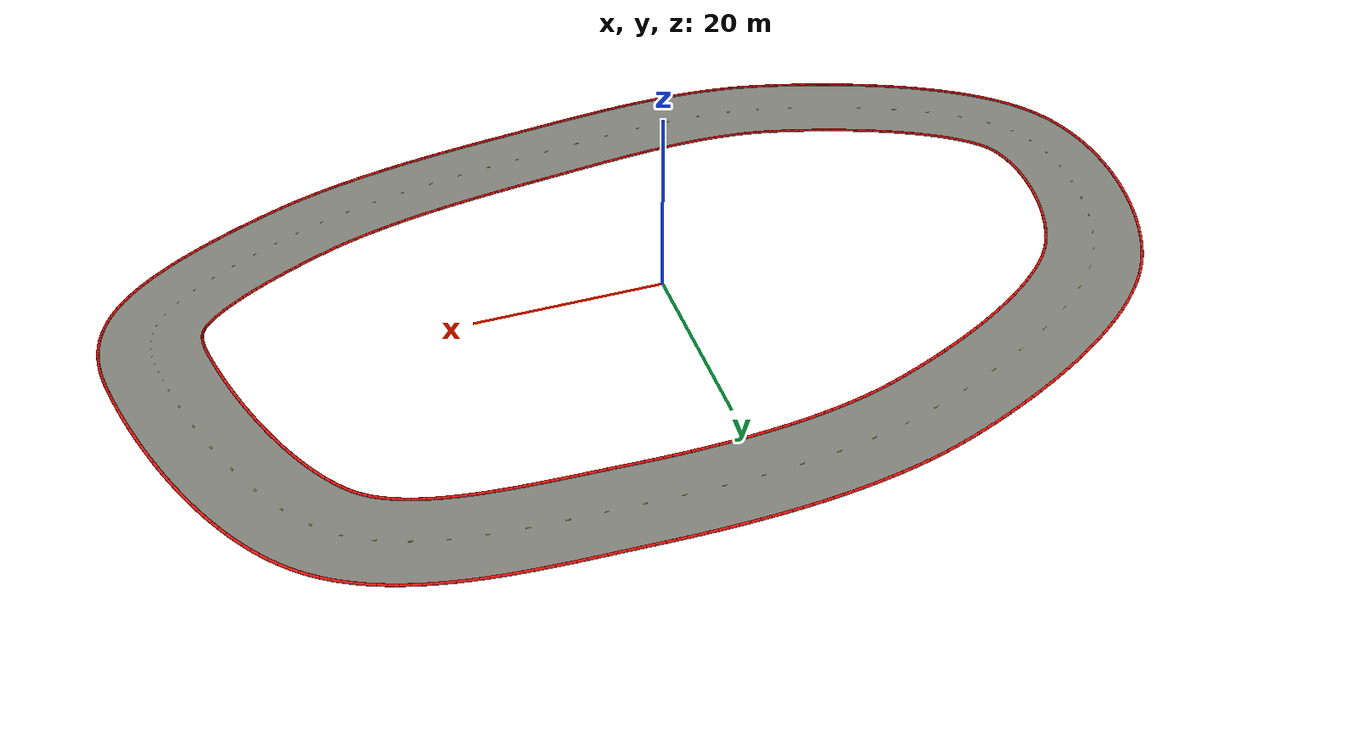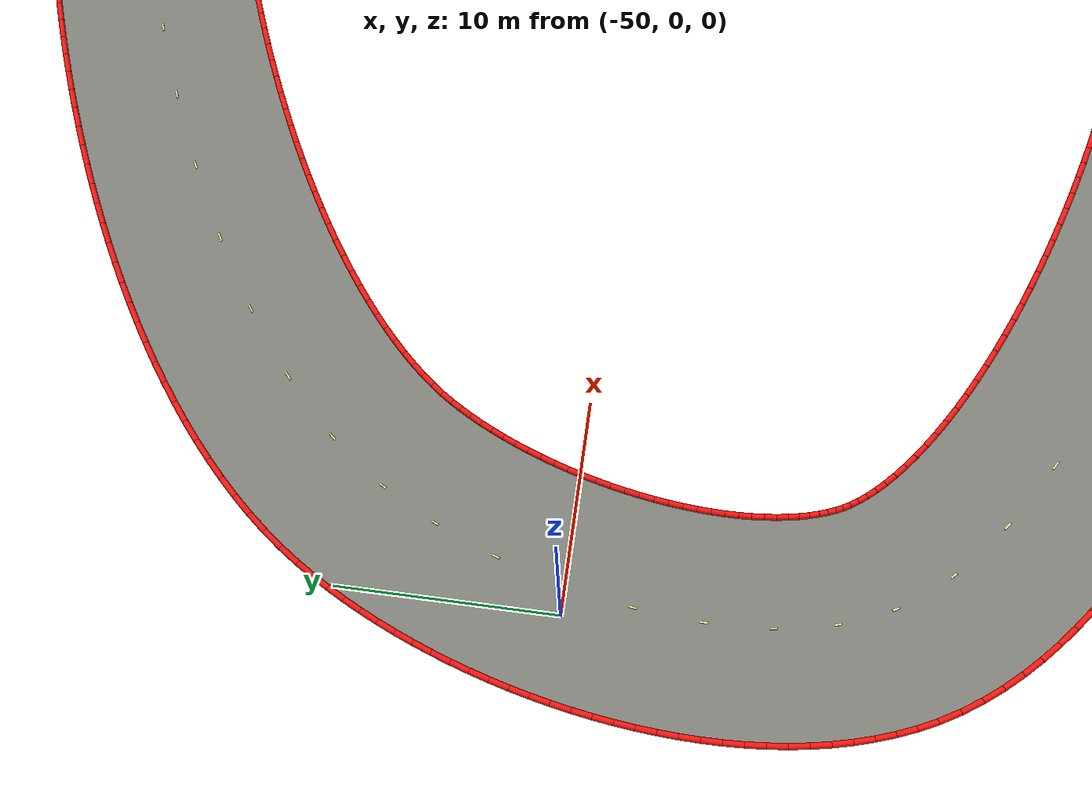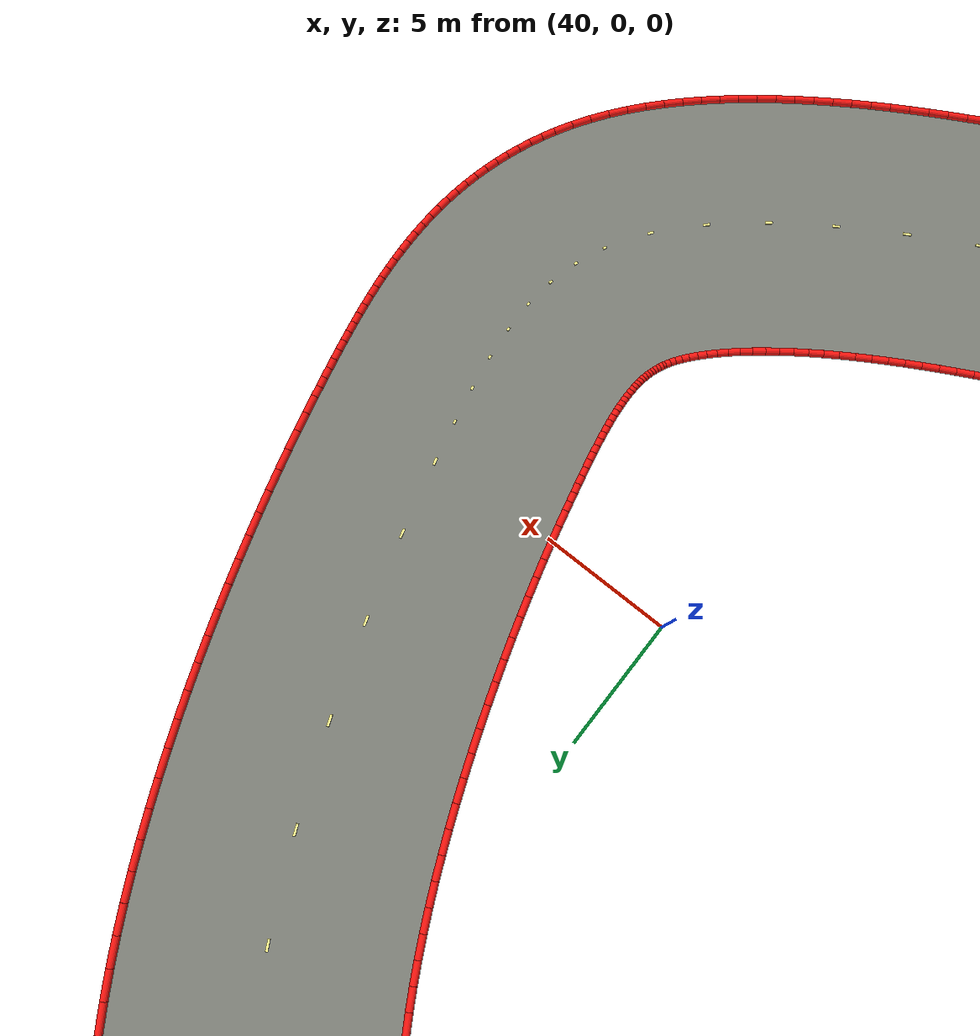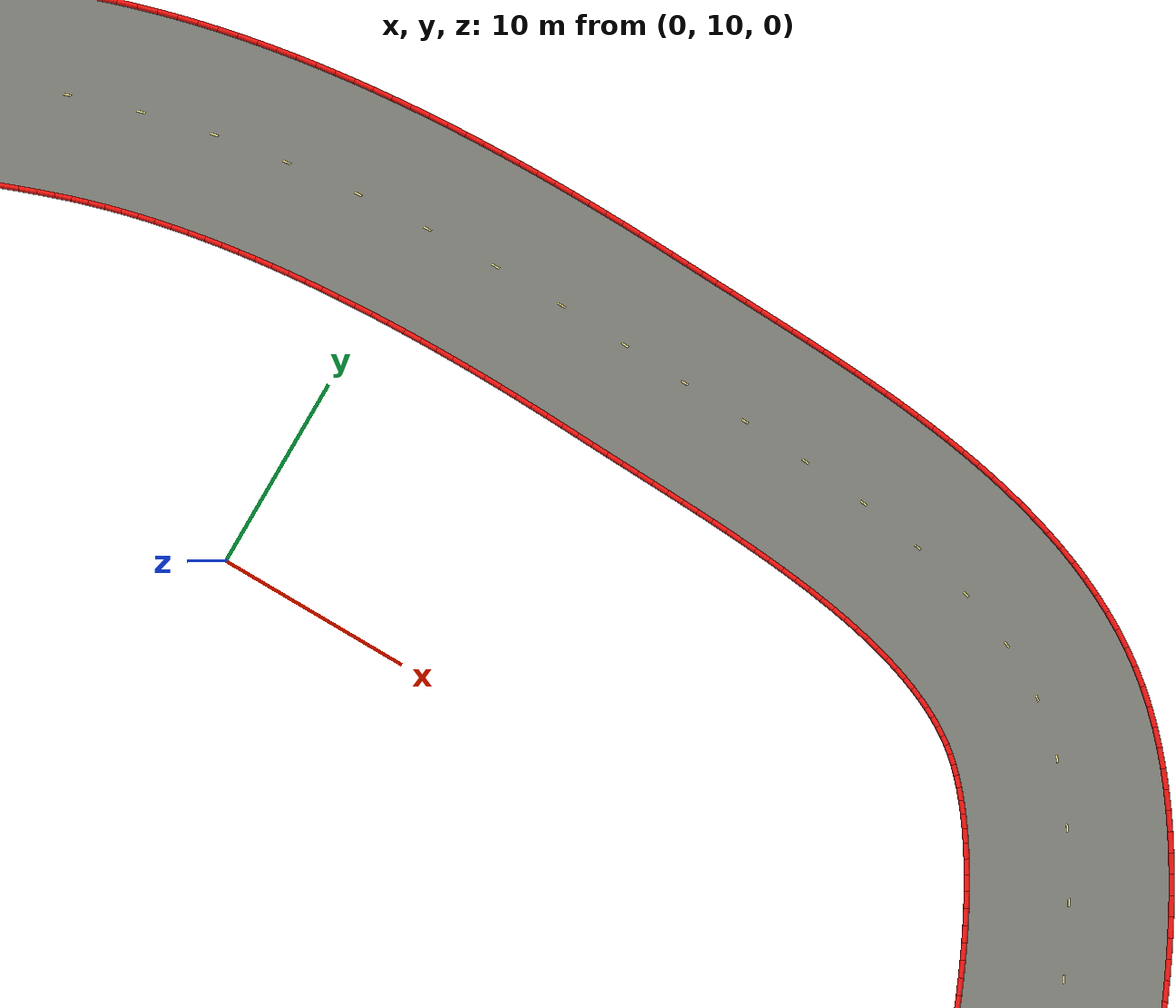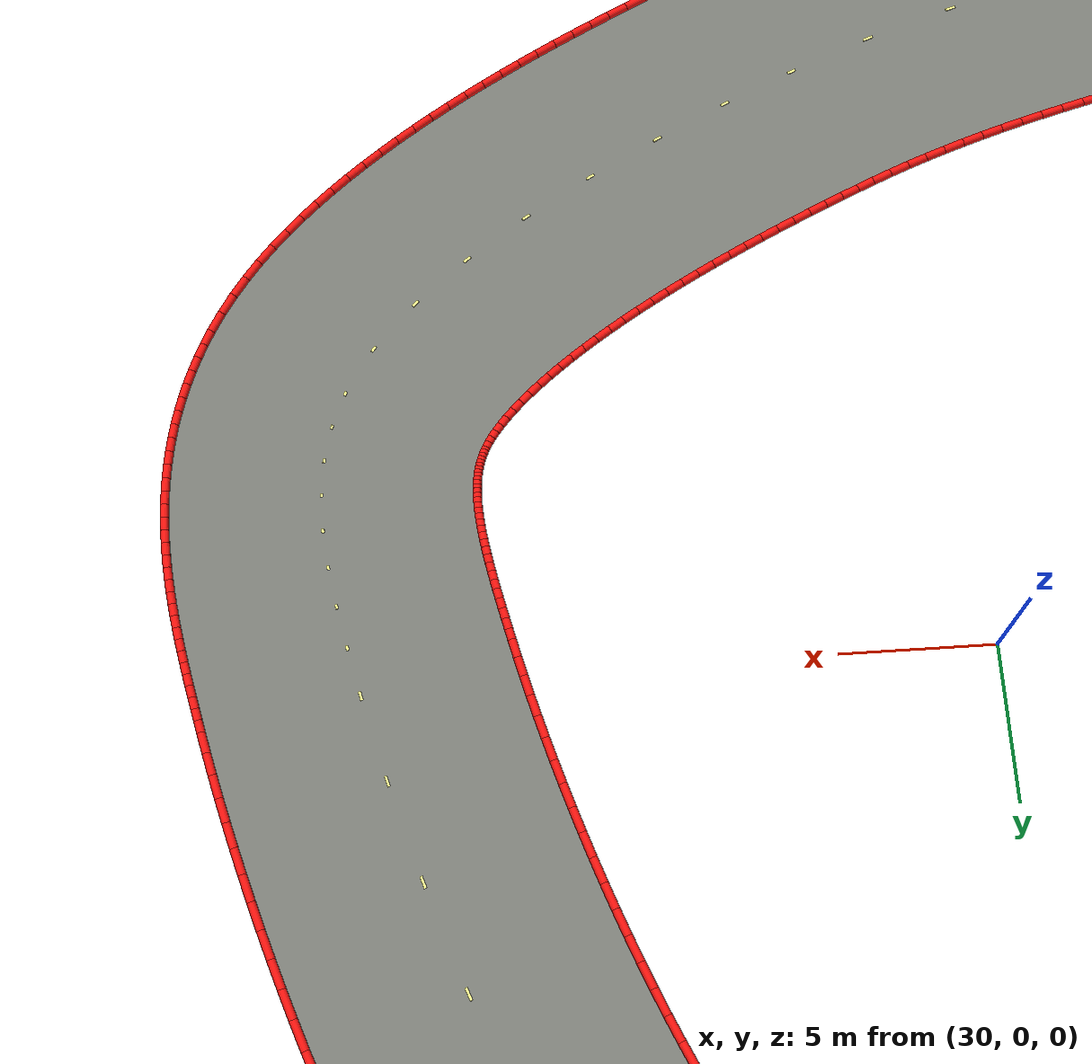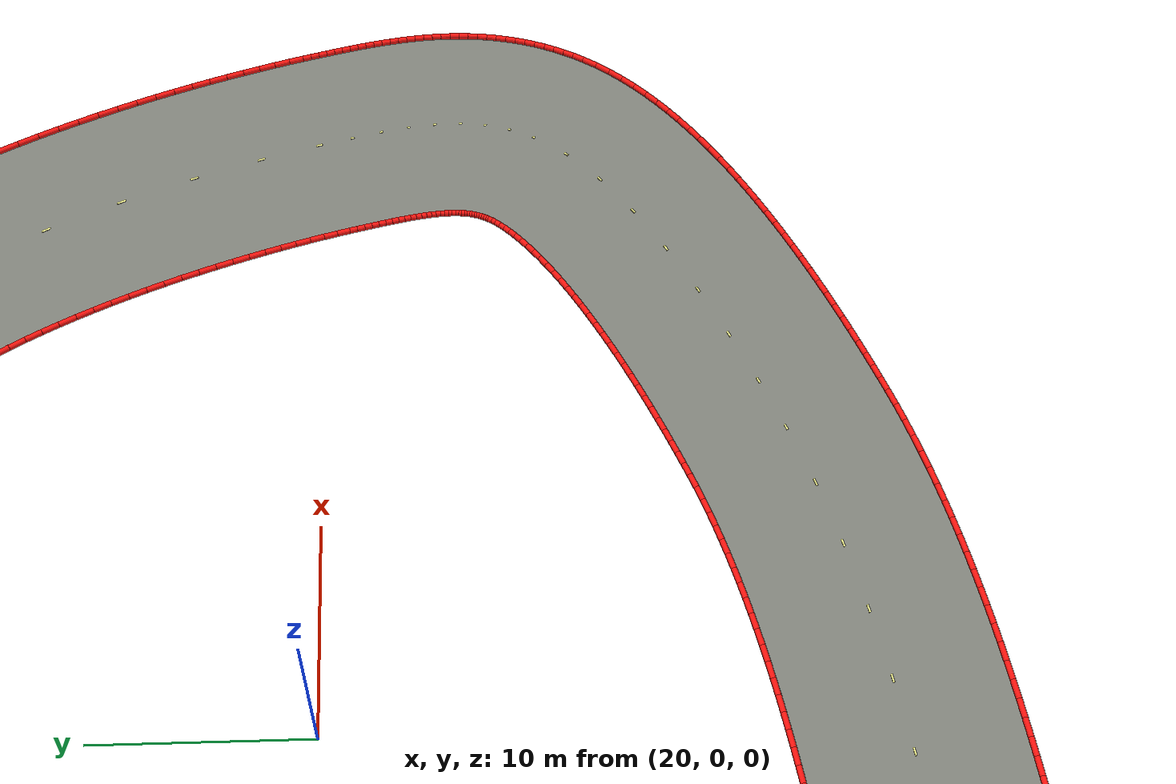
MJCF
<mujoco model="sweepers_track_visuals">
  <asset>
    <mesh name="track_surface_mesh" inertia="shell" vertex="45.13639 -1.15987 0.02200 44.99573 -0.57710 0.02200 44.84274 0.03033 0.02200 44.67495 0.67029 0.02200 44.49258 1.33966 0.02200 44.29579 2.03537 0.02200 44.08479 2.75445 0.02200 43.85977 3.49395 0.02200 43.62091 4.25095 0.02200 43.36844 5.02256 0.02200 43.10258 5.80589 0.02200 42.82356 6.59804 0.02200 42.53165 7.39611 0.02200 42.22714 8.19721 0.02200 41.91036 8.99842 0.02200 41.58166 9.79678 0.02200 41.24146 10.58936 0.02200 40.89022 11.37315 0.02200 40.52846 12.14516 0.02200 40.15681 12.90234 0.02200 39.77595 13.64163 0.02200 39.38672 14.35992 0.02200 38.99006 15.05411 0.02200 38.58709 15.72106 0.02200 38.17913 16.35763 0.02200 37.76770 16.96070 0.02200 37.35461 17.52722 0.02200 36.94196 18.05424 0.02200 36.53219 18.53898 0.02200 36.12810 18.97896 0.02200 35.73285 19.37210 0.02200 35.34992 19.71694 0.02200 34.97260 20.02070 0.02200 34.57852 20.30338 0.02200 34.15102 20.57927 0.02200 33.69497 20.84413 0.02200 33.20993 21.09780 0.02200 32.69583 21.33997 0.02200 32.15296 21.57030 0.02200 31.58189 21.78844 0.02200 30.98345 21.99409 0.02200 30.35865 22.18707 0.02200 29.70865 22.36728 0.02200 29.03474 22.53471 0.02200 28.33826 22.68951 0.02200 27.62061 22.83190 0.02200 26.88323 22.96220 0.02200 26.12754 23.08085 0.02200 25.35498 23.18834 0.02200 24.56698 23.28524 0.02200 23.76494 23.37220 0.02200 22.95023 23.44991 0.02200 22.12420 23.51912 0.02200 21.28817 23.58061 0.02200 20.44344 23.63522 0.02200 19.59124 23.68380 0.02200 18.73279 23.72725 0.02200 17.86927 23.76647 0.02200 17.00182 23.80243 0.02200 16.13154 23.83608 0.02200 15.25949 23.86840 0.02200 14.38668 23.90043 0.02200 13.51408 23.93318 0.02200 12.64262 23.96772 0.02200 11.78555 24.00460 0.02200 10.89341 24.04282 0.02200 10.00646 24.07638 0.02200 9.11431 24.10537 0.02200 8.21752 24.12938 0.02200 7.31666 24.14801 0.02200 6.41230 24.16087 0.02200 5.50501 24.16755 0.02200 4.59539 24.16767 0.02200 3.68400 24.16084 0.02200 2.77145 24.14668 0.02200 1.85832 24.12479 0.02200 0.94522 24.09481 0.02200 0.03274 24.05637 0.02200 -0.87851 24.00908 0.02200 -1.78793 23.95260 0.02200 -2.69490 23.88656 0.02200 -3.59881 23.81063 0.02200 -4.49905 23.72444 0.02200 -5.39500 23.62767 0.02200 -6.28606 23.52000 0.02200 -7.17160 23.40110 0.02200 -8.05100 23.27067 0.02200 -8.92366 23.12839 0.02200 -9.78897 22.97400 0.02200 -10.64631 22.80720 0.02200 -11.49509 22.62773 0.02200 -12.33472 22.43534 0.02200 -13.16460 22.22977 0.02200 -13.98417 22.01079 0.02200 -14.79286 21.77819 0.02200 -15.59013 21.53176 0.02200 -16.38781 21.26705 0.02200 -17.23731 20.96997 0.02200 -18.11426 20.65258 0.02200 -19.00462 20.31932 0.02200 -19.90614 19.97058 0.02200 -20.81663 19.60680 0.02200 -21.73387 19.22840 0.02200 -22.65568 18.83581 0.02200 -23.57989 18.42947 0.02200 -24.50430 18.00986 0.02200 -25.42675 17.57743 0.02200 -26.34505 17.13268 0.02200 -27.25703 16.67613 0.02200 -28.16049 16.20831 0.02200 -29.05324 15.72979 0.02200 -29.93308 15.24117 0.02200 -30.79779 14.74309 0.02200 -31.64515 14.23623 0.02200 -32.47294 13.72134 0.02200 -33.27890 13.19922 0.02200 -34.06081 12.67074 0.02200 -34.81639 12.13684 0.02200 -35.54343 11.59860 0.02200 -36.23967 11.05717 0.02200 -36.90292 10.51384 0.02200 -37.53101 9.97005 0.02200 -38.12185 9.42739 0.02200 -38.67345 8.88764 0.02200 -39.18396 8.35275 0.02200 -39.65174 7.82488 0.02200 -40.07543 7.30636 0.02200 -40.45403 6.79964 0.02200 -40.80006 6.28697 0.02200 -41.07939 5.83342 0.02200 -41.36547 5.33505 0.02200 -41.64584 4.81078 0.02200 -41.91896 4.26280 0.02200 -42.18347 3.69331 0.02200 -42.43812 3.10448 0.02200 -42.68179 2.49851 0.02200 -42.91345 1.87756 0.02200 -43.13216 1.24380 0.02200 -43.33704 0.59941 0.02200 -43.52731 -0.05347 0.02200 -43.70223 -0.71265 0.02200 -43.86112 -1.37596 0.02200 -44.00337 -2.04122 0.02200 -44.12842 -2.70620 0.02200 -44.23577 -3.36868 0.02200 -44.32499 -4.02640 0.02200 -44.39574 -4.67706 0.02200 -44.44774 -5.31835 0.02200 -44.48081 -5.94790 0.02200 -44.49488 -6.56331 0.02200 -44.49001 -7.16214 0.02200 -44.46640 -7.74194 0.02200 -44.42444 -8.30021 0.02200 -44.36470 -8.83448 0.02200 -44.28799 -9.34231 0.02200 -44.19539 -9.82132 0.02200 -44.08825 -10.26931 0.02200 -43.96823 -10.68426 0.02200 -43.83728 -11.06455 0.02200 -43.69762 -11.40899 0.02200 -43.55921 -11.70232 0.02200 -43.37589 -12.02943 0.02200 -43.15369 -12.36565 0.02200 -42.87856 -12.72880 0.02200 -42.54919 -13.11451 0.02200 -42.16562 -13.51831 0.02200 -41.72893 -13.93595 0.02200 -41.24095 -14.36358 0.02200 -40.70403 -14.79778 0.02200 -40.12086 -15.23560 0.02200 -39.49435 -15.67449 0.02200 -38.82752 -16.11225 0.02200 -38.12347 -16.54703 0.02200 -37.38530 -16.97722 0.02200 -36.61611 -17.40144 0.02200 -35.81900 -17.81851 0.02200 -34.99701 -18.22739 0.02200 -34.15318 -18.62717 0.02200 -33.29050 -19.01706 0.02200 -32.41192 -19.39635 0.02200 -31.52039 -19.76439 0.02200 -30.61881 -20.12061 0.02200 -29.71006 -20.46449 0.02200 -28.79703 -20.79555 0.02200 -27.88256 -21.11333 0.02200 -26.96951 -21.41742 0.02200 -26.06073 -21.70743 0.02200 -25.15907 -21.98299 0.02200 -24.26739 -22.24373 0.02200 -23.38858 -22.48933 0.02200 -22.52555 -22.71945 0.02200 -21.68125 -22.93377 0.02200 -20.87798 -23.12752 0.02200 -20.11134 -23.29610 0.02200 -19.34999 -23.44159 0.02200 -18.57398 -23.56908 0.02200 -17.78384 -23.67896 0.02200 -16.98014 -23.77164 0.02200 -16.16351 -23.84758 0.02200 -15.33460 -23.90724 0.02200 -14.49410 -23.95114 0.02200 -13.64272 -23.97983 0.02200 -12.78115 -23.99387 0.02200 -11.91013 -23.99387 0.02200 -11.03037 -23.98047 0.02200 -10.14261 -23.95433 0.02200 -9.24755 -23.91613 0.02200 -8.34593 -23.86657 0.02200 -7.43843 -23.80639 0.02200 -6.52577 -23.73632 0.02200 -5.60861 -23.65712 0.02200 -4.68765 -23.56957 0.02200 -3.76354 -23.47444 0.02200 -2.83692 -23.37255 0.02200 -1.90843 -23.26469 0.02200 -0.97868 -23.15169 0.02200 -0.04828 -23.03438 0.02200 0.88218 -22.91357 0.02200 1.81215 -22.79013 0.02200 2.74108 -22.66490 0.02200 3.66843 -22.53873 0.02200 4.59370 -22.41249 0.02200 5.51641 -22.28706 0.02200 6.43609 -22.16331 0.02200 7.34511 -22.04307 0.02200 8.18831 -21.93180 0.02200 9.02652 -21.81904 0.02200 9.86539 -21.70375 0.02200 10.70437 -21.58573 0.02200 11.54296 -21.46476 0.02200 12.38062 -21.34063 0.02200 13.21681 -21.21313 0.02200 14.05099 -21.08206 0.02200 14.88262 -20.94722 0.02200 15.71116 -20.80840 0.02200 16.53604 -20.66542 0.02200 17.35670 -20.51808 0.02200 18.17259 -20.36621 0.02200 18.98314 -20.20960 0.02200 19.78778 -20.04811 0.02200 20.58592 -19.88154 0.02200 21.37698 -19.70974 0.02200 22.16039 -19.53256 0.02200 22.93554 -19.34984 0.02200 23.70184 -19.16145 0.02200 24.45870 -18.96726 0.02200 25.20549 -18.76714 0.02200 25.94163 -18.56099 0.02200 26.66649 -18.34871 0.02200 27.37946 -18.13023 0.02200 28.07993 -17.90547 0.02200 28.76726 -17.67440 0.02200 29.44085 -17.43696 0.02200 30.10008 -17.19317 0.02200 30.74434 -16.94301 0.02200 31.37300 -16.68653 0.02200 32.00051 -16.41720 0.02200 32.55056 -16.17311 0.02200 33.11972 -15.91640 0.02200 33.69208 -15.65373 0.02200 34.26638 -15.38538 0.02200 34.84132 -15.11161 0.02200 35.41561 -14.83271 0.02200 35.98794 -14.54899 0.02200 36.55700 -14.26076 0.02200 37.12144 -13.96835 0.02200 37.67993 -13.67214 0.02200 38.23111 -13.37248 0.02200 38.77358 -13.06980 0.02200 39.30596 -12.76454 0.02200 39.82684 -12.45718 0.02200 40.33476 -12.14825 0.02200 40.82827 -11.83833 0.02200 41.30590 -11.52807 0.02200 41.76613 -11.21818 0.02200 42.20744 -10.90949 0.02200 42.62830 -10.60291 0.02200 43.02713 -10.29949 0.02200 43.40238 -10.00042 0.02200 43.75250 -9.70708 0.02200 44.07596 -9.42104 0.02200 44.37130 -9.14412 0.02200 44.63716 -8.87842 0.02200 44.87237 -8.62632 0.02200 45.07600 -8.39057 0.02200 45.24750 -8.17421 0.02200 45.38687 -7.98060 0.02200 45.49481 -7.81329 0.02200 45.58892 -7.64578 0.02200 45.63537 -7.55203 0.02200 45.68824 -7.43643 0.02200 45.73444 -7.32445 0.02200 45.77493 -7.21479 0.02200 45.81050 -7.10604 0.02200 45.84177 -6.99672 0.02200 45.86923 -6.88537 0.02200 45.89317 -6.77054 0.02200 45.91375 -6.65085 0.02200 45.93098 -6.52503 0.02200 45.94474 -6.39192 0.02200 45.95486 -6.25052 0.02200 45.96106 -6.09996 0.02200 45.96308 -5.93954 0.02200 45.96062 -5.76869 0.02200 45.95339 -5.58699 0.02200 45.94114 -5.39413 0.02200 45.92365 -5.18991 0.02200 45.90076 -4.97420 0.02200 45.87236 -4.74697 0.02200 45.83840 -4.50822 0.02200 45.79888 -4.25800 0.02200 45.75386 -3.99640 0.02200 45.70346 -3.72351 0.02200 45.64782 -3.43946 0.02200 45.58716 -3.14436 0.02200 45.52171 -2.83833 0.02200 45.45176 -2.52148 0.02200 45.37762 -2.19392 0.02200 45.29963 -1.85574 0.02200 45.21814 -1.50705 0.02200 54.86361 1.15987 0.02200 54.70477 1.81760 0.02200 54.52796 2.51959 0.02200 54.33575 3.25274 0.02200 54.12807 4.01496 0.02200 53.90486 4.80409 0.02200 53.66606 5.61791 0.02200 53.41159 6.45413 0.02200 53.14139 7.31045 0.02200 52.85537 8.18457 0.02200 52.55342 9.07414 0.02200 52.23544 9.97685 0.02200 51.90129 10.89037 0.02200 51.55079 11.81240 0.02200 51.18376 12.74063 0.02200 50.79994 13.67278 0.02200 50.39907 14.60661 0.02200 49.98079 15.53986 0.02200 49.54471 16.47035 0.02200 49.09034 17.39588 0.02200 48.61711 18.31431 0.02200 48.12430 19.22353 0.02200 47.61110 20.12142 0.02200 47.07652 21.00591 0.02200 46.51937 21.87491 0.02200 45.93823 22.72633 0.02200 45.33144 23.55800 0.02200 44.69701 24.36766 0.02200 44.03263 25.15287 0.02200 43.33562 25.91089 0.02200 42.60295 26.63859 0.02200 41.83126 27.33220 0.02200 41.02740 27.97930 0.02200 40.20997 28.56696 0.02200 39.37731 29.10487 0.02200 38.52679 29.59933 0.02200 37.66102 30.05256 0.02200 36.78226 30.46691 0.02200 35.89243 30.84480 0.02200 34.99314 31.18861 0.02200 34.08577 31.50070 0.02200 33.17149 31.78332 0.02200 32.25135 32.03861 0.02200 31.32625 32.26862 0.02200 30.39704 32.47529 0.02200 29.46451 32.66043 0.02200 28.52944 32.82577 0.02200 27.59259 32.97295 0.02200 26.65470 33.10351 0.02200 25.71656 33.21894 0.02200 24.77895 33.32065 0.02200 23.84270 33.41000 0.02200 22.90866 33.48830 0.02200 21.97769 33.55681 0.02200 21.05070 33.61676 0.02200 20.12866 33.66935 0.02200 19.21252 33.71573 0.02200 18.30332 33.75705 0.02200 17.40210 33.79441 0.02200 16.50996 33.82891 0.02200 15.62804 33.86161 0.02200 14.75752 33.89355 0.02200 13.89962 33.92574 0.02200 13.05562 33.95919 0.02200 12.21445 33.99540 0.02200 11.29637 34.03470 0.02200 10.35788 34.07020 0.02200 9.41047 34.10098 0.02200 8.45470 34.12656 0.02200 7.49109 34.14649 0.02200 6.52018 34.16028 0.02200 5.54249 34.16748 0.02200 4.55855 34.16761 0.02200 3.56888 34.16018 0.02200 2.57399 34.14473 0.02200 1.57439 34.12076 0.02200 0.57058 34.08779 0.02200 -0.43692 34.04533 0.02200 -1.44762 33.99287 0.02200 -2.46103 33.92992 0.02200 -3.47665 33.85596 0.02200 -4.49398 33.77048 0.02200 -5.51255 33.67295 0.02200 -6.53184 33.56284 0.02200 -7.55139 33.43962 0.02200 -8.57070 33.30274 0.02200 -9.58928 33.15164 0.02200 -10.60664 32.98576 0.02200 -11.62229 32.80451 0.02200 -12.63573 32.60731 0.02200 -13.64646 32.39357 0.02200 -14.65396 32.16267 0.02200 -15.65772 31.91400 0.02200 -16.65721 31.64692 0.02200 -17.65189 31.36078 0.02200 -18.64120 31.05494 0.02200 -19.61219 30.73295 0.02200 -20.58902 30.39155 0.02200 -21.56869 30.03698 0.02200 -22.56132 29.66543 0.02200 -23.56522 29.27710 0.02200 -24.57868 28.87217 0.02200 -25.59996 28.45084 0.02200 -26.62734 28.01328 0.02200 -27.65908 27.55966 0.02200 -28.69342 27.09013 0.02200 -29.72861 26.60483 0.02200 -30.76292 26.10388 0.02200 -31.79460 25.58738 0.02200 -32.82191 25.05540 0.02200 -33.84313 24.50800 0.02200 -34.85653 23.94517 0.02200 -35.86040 23.36689 0.02200 -36.85304 22.77309 0.02200 -37.83276 22.16364 0.02200 -38.79786 21.53835 0.02200 -39.74668 20.89696 0.02200 -40.67753 20.23913 0.02200 -41.58873 19.56442 0.02200 -42.47860 18.87227 0.02200 -43.34541 18.16200 0.02200 -44.18740 17.43279 0.02200 -45.00274 16.68366 0.02200 -45.78950 15.91344 0.02200 -46.54559 15.12080 0.02200 -47.26875 14.30418 0.02200 -47.95639 13.46188 0.02200 -48.60561 12.59203 0.02200 -49.19994 11.71303 0.02200 -49.67172 10.94926 0.02200 -50.11145 10.18354 0.02200 -50.53049 9.40022 0.02200 -50.92927 8.60035 0.02200 -51.30805 7.78500 0.02200 -51.66697 6.95524 0.02200 -52.00604 6.11214 0.02200 -52.32519 5.25679 0.02200 -52.62425 4.39027 0.02200 -52.90298 3.51367 0.02200 -53.16107 2.62809 0.02200 -53.39815 1.73462 0.02200 -53.61380 0.83432 0.02200 -53.80751 -0.07173 0.02200 -53.97874 -0.98248 0.02200 -54.12687 -1.89692 0.02200 -54.25123 -2.81405 0.02200 -54.35107 -3.73289 0.02200 -54.42555 -4.65253 0.02200 -54.47375 -5.57207 0.02200 -54.49462 -6.49064 0.02200 -54.48700 -7.40744 0.02200 -54.44958 -8.32166 0.02200 -54.38088 -9.23254 0.02200 -54.27920 -10.13929 0.02200 -54.14263 -11.04112 0.02200 -53.96900 -11.93711 0.02200 -53.75583 -12.82625 0.02200 -53.50036 -13.70726 0.02200 -53.19954 -14.57855 0.02200 -52.85004 -15.43802 0.02200 -52.44079 -16.29768 0.02200 -51.91640 -17.23133 0.02200 -51.32150 -18.13513 0.02200 -50.67517 -18.99082 0.02200 -49.98374 -19.80237 0.02200 -49.25219 -20.57384 0.02200 -48.48446 -21.30906 0.02200 -47.68374 -22.01148 0.02200 -46.85271 -22.68409 0.02200 -45.99367 -23.32943 0.02200 -45.10877 -23.94965 0.02200 -44.19998 -24.54651 0.02200 -43.26923 -25.12148 0.02200 -42.31845 -25.67573 0.02200 -41.34954 -26.21023 0.02200 -40.36444 -26.72576 0.02200 -39.36511 -27.22293 0.02200 -38.35355 -27.70225 0.02200 -37.33178 -28.16409 0.02200 -36.30186 -28.60875 0.02200 -35.26588 -29.03646 0.02200 -34.22596 -29.44737 0.02200 -33.18421 -29.84161 0.02200 -32.14280 -30.21923 0.02200 -31.10388 -30.58028 0.02200 -30.06963 -30.92475 0.02200 -29.04221 -31.25263 0.02200 -28.02380 -31.56387 0.02200 -27.01654 -31.85842 0.02200 -26.02257 -32.13620 0.02200 -25.04401 -32.39712 0.02200 -24.08291 -32.64109 0.02200 -23.12202 -32.87248 0.02200 -22.12280 -33.09172 0.02200 -21.09972 -33.28732 0.02200 -20.07388 -33.45595 0.02200 -19.04591 -33.59900 0.02200 -18.01638 -33.71781 0.02200 -16.98583 -33.81371 0.02200 -15.95474 -33.88800 0.02200 -14.92359 -33.94192 0.02200 -13.89283 -33.97670 0.02200 -12.86290 -33.99353 0.02200 -11.83424 -33.99358 0.02200 -10.80726 -33.97798 0.02200 -9.78241 -33.94784 0.02200 -8.76010 -33.90424 0.02200 -7.74080 -33.84825 0.02200 -6.72493 -33.78090 0.02200 -5.71295 -33.70323 0.02200 -4.70534 -33.61624 0.02200 -3.70257 -33.52093 0.02200 -2.70513 -33.41827 0.02200 -1.71353 -33.30925 0.02200 -0.72829 -33.19481 0.02200 0.25005 -33.07592 0.02200 1.22094 -32.95350 0.02200 2.18382 -32.82850 0.02200 3.13809 -32.70184 0.02200 4.08315 -32.57443 0.02200 5.01838 -32.44719 0.02200 5.94313 -32.32103 0.02200 6.85673 -32.19683 0.02200 7.75849 -32.07548 0.02200 8.65489 -31.95693 0.02200 9.50914 -31.84419 0.02200 10.37395 -31.72784 0.02200 11.24266 -31.60845 0.02200 12.11478 -31.48577 0.02200 12.98981 -31.35954 0.02200 13.86724 -31.22951 0.02200 14.74659 -31.09542 0.02200 15.62738 -30.95703 0.02200 16.50912 -30.81405 0.02200 17.39134 -30.66624 0.02200 18.27356 -30.51331 0.02200 19.15532 -30.35500 0.02200 20.03616 -30.19103 0.02200 20.91561 -30.02111 0.02200 21.79323 -29.84495 0.02200 22.66857 -29.66226 0.02200 23.54118 -29.47275 0.02200 24.41063 -29.27609 0.02200 25.27648 -29.07198 0.02200 26.13830 -28.86009 0.02200 26.99566 -28.64009 0.02200 27.84816 -28.41163 0.02200 28.69536 -28.17436 0.02200 29.53686 -27.92791 0.02200 30.37225 -27.67189 0.02200 31.20112 -27.40590 0.02200 32.02306 -27.12954 0.02200 32.83766 -26.84237 0.02200 33.64453 -26.54394 0.02200 34.44323 -26.23377 0.02200 35.23337 -25.91137 0.02200 35.99949 -25.58280 0.02200 36.63390 -25.30144 0.02200 37.26100 -25.01858 0.02200 37.89432 -24.72794 0.02200 38.53276 -24.42960 0.02200 39.17525 -24.12366 0.02200 39.82070 -23.81019 0.02200 40.46806 -23.48926 0.02200 41.11627 -23.16093 0.02200 41.76430 -22.82521 0.02200 42.41113 -22.48212 0.02200 43.05574 -22.13165 0.02200 43.69714 -21.77374 0.02200 44.33437 -21.40833 0.02200 44.96647 -21.03530 0.02200 45.59251 -20.65448 0.02200 46.21158 -20.26566 0.02200 46.82279 -19.86856 0.02200 47.42528 -19.46282 0.02200 48.01819 -19.04799 0.02200 48.60071 -18.62353 0.02200 49.17202 -18.18874 0.02200 49.73131 -17.74281 0.02200 50.27778 -17.28472 0.02200 50.81056 -16.81327 0.02200 51.32876 -16.32700 0.02200 51.83135 -15.82418 0.02200 52.31716 -15.30278 0.02200 52.78473 -14.76045 0.02200 53.23225 -14.19449 0.02200 53.65735 -13.60191 0.02200 54.05694 -12.97953 0.02200 54.41108 -12.35422 0.02200 54.65128 -11.87791 0.02200 54.85917 -11.42315 0.02200 55.04856 -10.96412 0.02200 55.21927 -10.50182 0.02200 55.37122 -10.03734 0.02200 55.50453 -9.57182 0.02200 55.61946 -9.10640 0.02200 55.71645 -8.64221 0.02200 55.79610 -8.18030 0.02200 55.85913 -7.72164 0.02200 55.90638 -7.26703 0.02200 55.93879 -6.81718 0.02200 55.95735 -6.37261 0.02200 55.96308 -5.93372 0.02200 55.95703 -5.50073 0.02200 55.94021 -5.07376 0.02200 55.91362 -4.65278 0.02200 55.87821 -4.23769 0.02200 55.83488 -3.82827 0.02200 55.78449 -3.42424 0.02200 55.72783 -3.02528 0.02200 55.66564 -2.63100 0.02200 55.59859 -2.24100 0.02200 55.52731 -1.85486 0.02200 55.45239 -1.47214 0.02200 55.37436 -1.09239 0.02200 55.29373 -0.71518 0.02200 55.21094 -0.34006 0.02200 55.12642 0.03339 0.02200 55.04059 0.40559 0.02200 54.95381 0.77696 0.02200" face="0 321 1 0 320 321 1 322 2 1 321 322 2 323 3 2 322 323 3 324 4 3 323 324 4 325 5 4 324 325 5 326 6 5 325 326 6 327 7 6 326 327 7 328 8 7 327 328 8 329 9 8 328 329 9 330 10 9 329 330 10 331 11 10 330 331 11 332 12 11 331 332 12 333 13 12 332 333 13 334 14 13 333 334 14 335 15 14 334 335 15 336 16 15 335 336 16 337 17 16 336 337 17 338 18 17 337 338 18 339 19 18 338 339 19 340 20 19 339 340 20 341 21 20 340 341 21 342 22 21 341 342 22 343 23 22 342 343 23 344 24 23 343 344 24 345 25 24 344 345 25 346 26 25 345 346 26 347 27 26 346 347 27 348 28 27 347 348 28 349 29 28 348 349 29 350 30 29 349 350 30 351 31 30 350 351 31 352 32 31 351 352 32 353 33 32 352 353 33 354 34 33 353 354 34 355 35 34 354 355 35 356 36 35 355 356 36 357 37 36 356 357 37 358 38 37 357 358 38 359 39 38 358 359 39 360 40 39 359 360 40 361 41 40 360 361 41 362 42 41 361 362 42 363 43 42 362 363 43 364 44 43 363 364 44 365 45 44 364 365 45 366 46 45 365 366 46 367 47 46 366 367 47 368 48 47 367 368 48 369 49 48 368 369 49 370 50 49 369 370 50 371 51 50 370 371 51 372 52 51 371 372 52 373 53 52 372 373 53 374 54 53 373 374 54 375 55 54 374 375 55 376 56 55 375 376 56 377 57 56 376 377 57 378 58 57 377 378 58 379 59 58 378 379 59 380 60 59 379 380 60 381 61 60 380 381 61 382 62 61 381 382 62 383 63 62 382 383 63 384 64 63 383 384 64 385 65 64 384 385 65 386 66 65 385 386 66 387 67 66 386 387 67 388 68 67 387 388 68 389 69 68 388 389 69 390 70 69 389 390 70 391 71 70 390 391 71 392 72 71 391 392 72 393 73 72 392 393 73 394 74 73 393 394 74 395 75 74 394 395 75 396 76 75 395 396 76 397 77 76 396 397 77 398 78 77 397 398 78 399 79 78 398 399 79 400 80 79 399 400 80 401 81 80 400 401 81 402 82 81 401 402 82 403 83 82 402 403 83 404 84 83 403 404 84 405 85 84 404 405 85 406 86 85 405 406 86 407 87 86 406 407 87 408 88 87 407 408 88 409 89 88 408 409 89 410 90 89 409 410 90 411 91 90 410 411 91 412 92 91 411 412 92 413 93 92 412 413 93 414 94 93 413 414 94 415 95 94 414 415 95 416 96 95 415 416 96 417 97 96 416 417 97 418 98 97 417 418 98 419 99 98 418 419 99 420 100 99 419 420 100 421 101 100 420 421 101 422 102 101 421 422 102 423 103 102 422 423 103 424 104 103 423 424 104 425 105 104 424 425 105 426 106 105 425 426 106 427 107 106 426 427 107 428 108 107 427 428 108 429 109 108 428 429 109 430 110 109 429 430 110 431 111 110 430 431 111 432 112 111 431 432 112 433 113 112 432 433 113 434 114 113 433 434 114 435 115 114 434 435 115 436 116 115 435 436 116 437 117 116 436 437 117 438 118 117 437 438 118 439 119 118 438 439 119 440 120 119 439 440 120 441 121 120 440 441 121 442 122 121 441 442 122 443 123 122 442 443 123 444 124 123 443 444 124 445 125 124 444 445 125 446 126 125 445 446 126 447 127 126 446 447 127 448 128 127 447 448 128 449 129 128 448 449 129 450 130 129 449 450 130 451 131 130 450 451 131 452 132 131 451 452 132 453 133 132 452 453 133 454 134 133 453 454 134 455 135 134 454 455 135 456 136 135 455 456 136 457 137 136 456 457 137 458 138 137 457 458 138 459 139 138 458 459 139 460 140 139 459 460 140 461 141 140 460 461 141 462 142 141 461 462 142 463 143 142 462 463 143 464 144 143 463 464 144 465 145 144 464 465 145 466 146 145 465 466 146 467 147 146 466 467 147 468 148 147 467 468 148 469 149 148 468 469 149 470 150 149 469 470 150 471 151 150 470 471 151 472 152 151 471 472 152 473 153 152 472 473 153 474 154 153 473 474 154 475 155 154 474 475 155 476 156 155 475 476 156 477 157 156 476 477 157 478 158 157 477 478 158 479 159 158 478 479 159 480 160 159 479 480 160 481 161 160 480 481 161 482 162 161 481 482 162 483 163 162 482 483 163 484 164 163 483 484 164 485 165 164 484 485 165 486 166 165 485 486 166 487 167 166 486 487 167 488 168 167 487 488 168 489 169 168 488 489 169 490 170 169 489 490 170 491 171 170 490 491 171 492 172 171 491 492 172 493 173 172 492 493 173 494 174 173 493 494 174 495 175 174 494 495 175 496 176 175 495 496 176 497 177 176 496 497 177 498 178 177 497 498 178 499 179 178 498 499 179 500 180 179 499 500 180 501 181 180 500 501 181 502 182 181 501 502 182 503 183 182 502 503 183 504 184 183 503 504 184 505 185 184 504 505 185 506 186 185 505 506 186 507 187 186 506 507 187 508 188 187 507 508 188 509 189 188 508 509 189 510 190 189 509 510 190 511 191 190 510 511 191 512 192 191 511 512 192 513 193 192 512 513 193 514 194 193 513 514 194 515 195 194 514 515 195 516 196 195 515 516 196 517 197 196 516 517 197 518 198 197 517 518 198 519 199 198 518 519 199 520 200 199 519 520 200 521 201 200 520 521 201 522 202 201 521 522 202 523 203 202 522 523 203 524 204 203 523 524 204 525 205 204 524 525 205 526 206 205 525 526 206 527 207 206 526 527 207 528 208 207 527 528 208 529 209 208 528 529 209 530 210 209 529 530 210 531 211 210 530 531 211 532 212 211 531 532 212 533 213 212 532 533 213 534 214 213 533 534 214 535 215 214 534 535 215 536 216 215 535 536 216 537 217 216 536 537 217 538 218 217 537 538 218 539 219 218 538 539 219 540 220 219 539 540 220 541 221 220 540 541 221 542 222 221 541 542 222 543 223 222 542 543 223 544 224 223 543 544 224 545 225 224 544 545 225 546 226 225 545 546 226 547 227 226 546 547 227 548 228 227 547 548 228 549 229 228 548 549 229 550 230 229 549 550 230 551 231 230 550 551 231 552 232 231 551 552 232 553 233 232 552 553 233 554 234 233 553 554 234 555 235 234 554 555 235 556 236 235 555 556 236 557 237 236 556 557 237 558 238 237 557 558 238 559 239 238 558 559 239 560 240 239 559 560 240 561 241 240 560 561 241 562 242 241 561 562 242 563 243 242 562 563 243 564 244 243 563 564 244 565 245 244 564 565 245 566 246 245 565 566 246 567 247 246 566 567 247 568 248 247 567 568 248 569 249 248 568 569 249 570 250 249 569 570 250 571 251 250 570 571 251 572 252 251 571 572 252 573 253 252 572 573 253 574 254 253 573 574 254 575 255 254 574 575 255 576 256 255 575 576 256 577 257 256 576 577 257 578 258 257 577 578 258 579 259 258 578 579 259 580 260 259 579 580 260 581 261 260 580 581 261 582 262 261 581 582 262 583 263 262 582 583 263 584 264 263 583 584 264 585 265 264 584 585 265 586 266 265 585 586 266 587 267 266 586 587 267 588 268 267 587 588 268 589 269 268 588 589 269 590 270 269 589 590 270 591 271 270 590 591 271 592 272 271 591 592 272 593 273 272 592 593 273 594 274 273 593 594 274 595 275 274 594 595 275 596 276 275 595 596 276 597 277 276 596 597 277 598 278 277 597 598 278 599 279 278 598 599 279 600 280 279 599 600 280 601 281 280 600 601 281 602 282 281 601 602 282 603 283 282 602 603 283 604 284 283 603 604 284 605 285 284 604 605 285 606 286 285 605 606 286 607 287 286 606 607 287 608 288 287 607 608 288 609 289 288 608 609 289 610 290 289 609 610 290 611 291 290 610 611 291 612 292 291 611 612 292 613 293 292 612 613 293 614 294 293 613 614 294 615 295 294 614 615 295 616 296 295 615 616 296 617 297 296 616 617 297 618 298 297 617 618 298 619 299 298 618 619 299 620 300 299 619 620 300 621 301 300 620 621 301 622 302 301 621 622 302 623 303 302 622 623 303 624 304 303 623 624 304 625 305 304 624 625 305 626 306 305 625 626 306 627 307 306 626 627 307 628 308 307 627 628 308 629 309 308 628 629 309 630 310 309 629 630 310 631 311 310 630 631 311 632 312 311 631 632 312 633 313 312 632 633 313 634 314 313 633 634 314 635 315 314 634 635 315 636 316 315 635 636 316 637 317 316 636 637 317 638 318 317 637 638 318 639 319 318 638 639 319 320 0 319 639 320"/>
    <material name="track_asphalt" rgba="0.48 0.49 0.46 1" emission="0.08"/>
    <material name="track_boundary" rgba="0.95 0.08 0.06 1" emission="0.05"/>
    <material name="track_centerline" rgba="1.0 0.95 0.55 1" emission="0.15"/>
  </asset>
  <worldbody>
    <geom name="track_surface" type="mesh" mesh="track_surface_mesh" material="track_asphalt" contype="0" conaffinity="0"/>
    <geom name="track_left_boundary_000" type="capsule" fromto="45.13639 -1.15987 0.09 44.99573 -0.57710 0.09" size="0.14" material="track_boundary" contype="0" conaffinity="0"/>
    <geom name="track_left_boundary_001" type="capsule" fromto="44.99573 -0.57710 0.09 44.84274 0.03033 0.09" size="0.14" material="track_boundary" contype="0" conaffinity="0"/>
    <geom name="track_left_boundary_002" type="capsule" fromto="44.84274 0.03033 0.09 44.67495 0.67029 0.09" size="0.14" material="track_boundary" contype="0" conaffinity="0"/>
    <geom name="track_left_boundary_003" type="capsule" fromto="44.67495 0.67029 0.09 44.49258 1.33966 0.09" size="0.14" material="track_boundary" contype="0" conaffinity="0"/>
    <geom name="track_left_boundary_004" type="capsule" fromto="44.49258 1.33966 0.09 44.29579 2.03537 0.09" size="0.14" material="track_boundary" contype="0" conaffinity="0"/>
    <geom name="track_left_boundary_005" type="capsule" fromto="44.29579 2.03537 0.09 44.08479 2.75445 0.09" size="0.14" material="track_boundary" contype="0" conaffinity="0"/>
    <geom name="track_left_boundary_006" type="capsule" fromto="44.08479 2.75445 0.09 43.85977 3.49395 0.09" size="0.14" material="track_boundary" contype="0" conaffinity="0"/>
    <geom name="track_left_boundary_007" type="capsule" fromto="43.85977 3.49395 0.09 43.62091 4.25095 0.09" size="0.14" material="track_boundary" contype="0" conaffinity="0"/>
    <geom name="track_left_boundary_008" type="capsule" fromto="43.62091 4.25095 0.09 43.36844 5.02256 0.09" size="0.14" material="track_boundary" contype="0" conaffinity="0"/>
    <geom name="track_left_boundary_009" type="capsule" fromto="43.36844 5.02256 0.09 43.10258 5.80589 0.09" size="0.14" material="track_boundary" contype="0" conaffinity="0"/>
    <geom name="track_left_boundary_010" type="capsule" fromto="43.10258 5.80589 0.09 42.82356 6.59804 0.09" size="0.14" material="track_boundary" contype="0" conaffinity="0"/>
    <geom name="track_left_boundary_011" type="capsule" fromto="42.82356 6.59804 0.09 42.53165 7.39611 0.09" size="0.14" material="track_boundary" contype="0" conaffinity="0"/>
    <geom name="track_left_boundary_012" type="capsule" fromto="42.53165 7.39611 0.09 42.22714 8.19721 0.09" size="0.14" material="track_boundary" contype="0" conaffinity="0"/>
    <geom name="track_left_boundary_013" type="capsule" fromto="42.22714 8.19721 0.09 41.91036 8.99842 0.09" size="0.14" material="track_boundary" contype="0" conaffinity="0"/>
    <geom name="track_left_boundary_014" type="capsule" fromto="41.91036 8.99842 0.09 41.58166 9.79678 0.09" size="0.14" material="track_boundary" contype="0" conaffinity="0"/>
    <geom name="track_left_boundary_015" type="capsule" fromto="41.58166 9.79678 0.09 41.24146 10.58936 0.09" size="0.14" material="track_boundary" contype="0" conaffinity="0"/>
    <geom name="track_left_boundary_016" type="capsule" fromto="41.24146 10.58936 0.09 40.89022 11.37315 0.09" size="0.14" material="track_boundary" contype="0" conaffinity="0"/>
    <geom name="track_left_boundary_017" type="capsule" fromto="40.89022 11.37315 0.09 40.52846 12.14516 0.09" size="0.14" material="track_boundary" contype="0" conaffinity="0"/>
    <geom name="track_left_boundary_018" type="capsule" fromto="40.52846 12.14516 0.09 40.15681 12.90234 0.09" size="0.14" material="track_boundary" contype="0" conaffinity="0"/>
    <geom name="track_left_boundary_019" type="capsule" fromto="40.15681 12.90234 0.09 39.77595 13.64163 0.09" size="0.14" material="track_boundary" contype="0" conaffinity="0"/>
    <geom name="track_left_boundary_020" type="capsule" fromto="39.77595 13.64163 0.09 39.38672 14.35992 0.09" size="0.14" material="track_boundary" contype="0" conaffinity="0"/>
    <geom name="track_left_boundary_021" type="capsule" fromto="39.38672 14.35992 0.09 38.99006 15.05411 0.09" size="0.14" material="track_boundary" contype="0" conaffinity="0"/>
    <geom name="track_left_boundary_022" type="capsule" fromto="38.99006 15.05411 0.09 38.58709 15.72106 0.09" size="0.14" material="track_boundary" contype="0" conaffinity="0"/>
    <geom name="track_left_boundary_023" type="capsule" fromto="38.58709 15.72106 0.09 38.17913 16.35763 0.09" size="0.14" material="track_boundary" contype="0" conaffinity="0"/>
    <geom name="track_left_boundary_024" type="capsule" fromto="38.17913 16.35763 0.09 37.76770 16.96070 0.09" size="0.14" material="track_boundary" contype="0" conaffinity="0"/>
    <geom name="track_left_boundary_025" type="capsule" fromto="37.76770 16.96070 0.09 37.35461 17.52722 0.09" size="0.14" material="track_boundary" contype="0" conaffinity="0"/>
    <geom name="track_left_boundary_026" type="capsule" fromto="37.35461 17.52722 0.09 36.94196 18.05424 0.09" size="0.14" material="track_boundary" contype="0" conaffinity="0"/>
    <geom name="track_left_boundary_027" type="capsule" fromto="36.94196 18.05424 0.09 36.53219 18.53898 0.09" size="0.14" material="track_boundary" contype="0" conaffinity="0"/>
    <geom name="track_left_boundary_028" type="capsule" fromto="36.53219 18.53898 0.09 36.12810 18.97896 0.09" size="0.14" material="track_boundary" contype="0" conaffinity="0"/>
    <geom name="track_left_boundary_029" type="capsule" fromto="36.12810 18.97896 0.09 35.73285 19.37210 0.09" size="0.14" material="track_boundary" contype="0" conaffinity="0"/>
    <geom name="track_left_boundary_030" type="capsule" fromto="35.73285 19.37210 0.09 35.34992 19.71694 0.09" size="0.14" material="track_boundary" contype="0" conaffinity="0"/>
    <geom name="track_left_boundary_031" type="capsule" fromto="35.34992 19.71694 0.09 34.97260 20.02070 0.09" size="0.14" material="track_boundary" contype="0" conaffinity="0"/>
    <geom name="track_left_boundary_032" type="capsule" fromto="34.97260 20.02070 0.09 34.57852 20.30338 0.09" size="0.14" material="track_boundary" contype="0" conaffinity="0"/>
    <geom name="track_left_boundary_033" type="capsule" fromto="34.57852 20.30338 0.09 34.15102 20.57927 0.09" size="0.14" material="track_boundary" contype="0" conaffinity="0"/>
    <geom name="track_left_boundary_034" type="capsule" fromto="34.15102 20.57927 0.09 33.69497 20.84413 0.09" size="0.14" material="track_boundary" contype="0" conaffinity="0"/>
    <geom name="track_left_boundary_035" type="capsule" fromto="33.69497 20.84413 0.09 33.20993 21.09780 0.09" size="0.14" material="track_boundary" contype="0" conaffinity="0"/>
    <geom name="track_left_boundary_036" type="capsule" fromto="33.20993 21.09780 0.09 32.69583 21.33997 0.09" size="0.14" material="track_boundary" contype="0" conaffinity="0"/>
    <geom name="track_left_boundary_037" type="capsule" fromto="32.69583 21.33997 0.09 32.15296 21.57030 0.09" size="0.14" material="track_boundary" contype="0" conaffinity="0"/>
    <geom name="track_left_boundary_038" type="capsule" fromto="32.15296 21.57030 0.09 31.58189 21.78844 0.09" size="0.14" material="track_boundary" contype="0" conaffinity="0"/>
    <geom name="track_left_boundary_039" type="capsule" fromto="31.58189 21.78844 0.09 30.98345 21.99409 0.09" size="0.14" material="track_boundary" contype="0" conaffinity="0"/>
    <geom name="track_left_boundary_040" type="capsule" fromto="30.98345 21.99409 0.09 30.35865 22.18707 0.09" size="0.14" material="track_boundary" contype="0" conaffinity="0"/>
    <geom name="track_left_boundary_041" type="capsule" fromto="30.35865 22.18707 0.09 29.70865 22.36728 0.09" size="0.14" material="track_boundary" contype="0" conaffinity="0"/>
    <geom name="track_left_boundary_042" type="capsule" fromto="29.70865 22.36728 0.09 29.03474 22.53471 0.09" size="0.14" material="track_boundary" contype="0" conaffinity="0"/>
    <geom name="track_left_boundary_043" type="capsule" fromto="29.03474 22.53471 0.09 28.33826 22.68951 0.09" size="0.14" material="track_boundary" contype="0" conaffinity="0"/>
    <geom name="track_left_boundary_044" type="capsule" fromto="28.33826 22.68951 0.09 27.62061 22.83190 0.09" size="0.14" material="track_boundary" contype="0" conaffinity="0"/>
    <geom name="track_left_boundary_045" type="capsule" fromto="27.62061 22.83190 0.09 26.88323 22.96220 0.09" size="0.14" material="track_boundary" contype="0" conaffinity="0"/>
    <geom name="track_left_boundary_046" type="capsule" fromto="26.88323 22.96220 0.09 26.12754 23.08085 0.09" size="0.14" material="track_boundary" contype="0" conaffinity="0"/>
    <geom name="track_left_boundary_047" type="capsule" fromto="26.12754 23.08085 0.09 25.35498 23.18834 0.09" size="0.14" material="track_boundary" contype="0" conaffinity="0"/>
    <geom name="track_left_boundary_048" type="capsule" fromto="25.35498 23.18834 0.09 24.56698 23.28524 0.09" size="0.14" material="track_boundary" contype="0" conaffinity="0"/>
    <geom name="track_left_boundary_049" type="capsule" fromto="24.56698 23.28524 0.09 23.76494 23.37220 0.09" size="0.14" material="track_boundary" contype="0" conaffinity="0"/>
    <geom name="track_left_boundary_050" type="capsule" fromto="23.76494 23.37220 0.09 22.95023 23.44991 0.09" size="0.14" material="track_boundary" contype="0" conaffinity="0"/>
    <geom name="track_left_boundary_051" type="capsule" fromto="22.95023 23.44991 0.09 22.12420 23.51912 0.09" size="0.14" material="track_boundary" contype="0" conaffinity="0"/>
    <geom name="track_left_boundary_052" type="capsule" fromto="22.12420 23.51912 0.09 21.28817 23.58061 0.09" size="0.14" material="track_boundary" contype="0" conaffinity="0"/>
    <geom name="track_left_boundary_053" type="capsule" fromto="21.28817 23.58061 0.09 20.44344 23.63522 0.09" size="0.14" material="track_boundary" contype="0" conaffinity="0"/>
    <geom name="track_left_boundary_054" type="capsule" fromto="20.44344 23.63522 0.09 19.59124 23.68380 0.09" size="0.14" material="track_boundary" contype="0" conaffinity="0"/>
    <geom name="track_left_boundary_055" type="capsule" fromto="19.59124 23.68380 0.09 18.73279 23.72725 0.09" size="0.14" material="track_boundary" contype="0" conaffinity="0"/>
    <geom name="track_left_boundary_056" type="capsule" fromto="18.73279 23.72725 0.09 17.86927 23.76647 0.09" size="0.14" material="track_boundary" contype="0" conaffinity="0"/>
    <geom name="track_left_boundary_057" type="capsule" fromto="17.86927 23.76647 0.09 17.00182 23.80243 0.09" size="0.14" material="track_boundary" contype="0" conaffinity="0"/>
    <geom name="track_left_boundary_058" type="capsule" fromto="17.00182 23.80243 0.09 16.13154 23.83608 0.09" size="0.14" material="track_boundary" contype="0" conaffinity="0"/>
    <geom name="track_left_boundary_059" type="capsule" fromto="16.13154 23.83608 0.09 15.25949 23.86840 0.09" size="0.14" material="track_boundary" contype="0" conaffinity="0"/>
    <geom name="track_left_boundary_060" type="capsule" fromto="15.25949 23.86840 0.09 14.38668 23.90043 0.09" size="0.14" material="track_boundary" contype="0" conaffinity="0"/>
    <geom name="track_left_boundary_061" type="capsule" fromto="14.38668 23.90043 0.09 13.51408 23.93318 0.09" size="0.14" material="track_boundary" contype="0" conaffinity="0"/>
    <geom name="track_left_boundary_062" type="capsule" fromto="13.51408 23.93318 0.09 12.64262 23.96772 0.09" size="0.14" material="track_boundary" contype="0" conaffinity="0"/>
    <geom name="track_left_boundary_063" type="capsule" fromto="12.64262 23.96772 0.09 11.78555 24.00460 0.09" size="0.14" material="track_boundary" contype="0" conaffinity="0"/>
    <geom name="track_left_boundary_064" type="capsule" fromto="11.78555 24.00460 0.09 10.89341 24.04282 0.09" size="0.14" material="track_boundary" contype="0" conaffinity="0"/>
    <geom name="track_left_boundary_065" type="capsule" fromto="10.89341 24.04282 0.09 10.00646 24.07638 0.09" size="0.14" material="track_boundary" contype="0" conaffinity="0"/>
    <geom name="track_left_boundary_066" type="capsule" fromto="10.00646 24.07638 0.09 9.11431 24.10537 0.09" size="0.14" material="track_boundary" contype="0" conaffinity="0"/>
    <geom name="track_left_boundary_067" type="capsule" fromto="9.11431 24.10537 0.09 8.21752 24.12938 0.09" size="0.14" material="track_boundary" contype="0" conaffinity="0"/>
    <geom name="track_left_boundary_068" type="capsule" fromto="8.21752 24.12938 0.09 7.31666 24.14801 0.09" size="0.14" material="track_boundary" contype="0" conaffinity="0"/>
    <geom name="track_left_boundary_069" type="capsule" fromto="7.31666 24.14801 0.09 6.41230 24.16087 0.09" size="0.14" material="track_boundary" contype="0" conaffinity="0"/>
    <geom name="track_left_boundary_070" type="capsule" fromto="6.41230 24.16087 0.09 5.50501 24.16755 0.09" size="0.14" material="track_boundary" contype="0" conaffinity="0"/>
    <geom name="track_left_boundary_071" type="capsule" fromto="5.50501 24.16755 0.09 4.59539 24.16767 0.09" size="0.14" material="track_boundary" contype="0" conaffinity="0"/>
    <geom name="track_left_boundary_072" type="capsule" fromto="4.59539 24.16767 0.09 3.68400 24.16084 0.09" size="0.14" material="track_boundary" contype="0" conaffinity="0"/>
    <geom name="track_left_boundary_073" type="capsule" fromto="3.68400 24.16084 0.09 2.77145 24.14668 0.09" size="0.14" material="track_boundary" contype="0" conaffinity="0"/>
    <geom name="track_left_boundary_074" type="capsule" fromto="2.77145 24.14668 0.09 1.85832 24.12479 0.09" size="0.14" material="track_boundary" contype="0" conaffinity="0"/>
    <geom name="track_left_boundary_075" type="capsule" fromto="1.85832 24.12479 0.09 0.94522 24.09481 0.09" size="0.14" material="track_boundary" contype="0" conaffinity="0"/>
    <geom name="track_left_boundary_076" type="capsule" fromto="0.94522 24.09481 0.09 0.03274 24.05637 0.09" size="0.14" material="track_boundary" contype="0" conaffinity="0"/>
    <geom name="track_left_boundary_077" type="capsule" fromto="0.03274 24.05637 0.09 -0.87851 24.00908 0.09" size="0.14" material="track_boundary" contype="0" conaffinity="0"/>
    <geom name="track_left_boundary_078" type="capsule" fromto="-0.87851 24.00908 0.09 -1.78793 23.95260 0.09" size="0.14" material="track_boundary" contype="0" conaffinity="0"/>
    <geom name="track_left_boundary_079" type="capsule" fromto="-1.78793 23.95260 0.09 -2.69490 23.88656 0.09" size="0.14" material="track_boundary" contype="0" conaffinity="0"/>
    <geom name="track_left_boundary_080" type="capsule" fromto="-2.69490 23.88656 0.09 -3.59881 23.81063 0.09" size="0.14" material="track_boundary" contype="0" conaffinity="0"/>
    <geom name="track_left_boundary_081" type="capsule" fromto="-3.59881 23.81063 0.09 -4.49905 23.72444 0.09" size="0.14" material="track_boundary" contype="0" conaffinity="0"/>
    <geom name="track_left_boundary_082" type="capsule" fromto="-4.49905 23.72444 0.09 -5.39500 23.62767 0.09" size="0.14" material="track_boundary" contype="0" conaffinity="0"/>
    <geom name="track_left_boundary_083" type="capsule" fromto="-5.39500 23.62767 0.09 -6.28606 23.52000 0.09" size="0.14" material="track_boundary" contype="0" conaffinity="0"/>
    <geom name="track_left_boundary_084" type="capsule" fromto="-6.28606 23.52000 0.09 -7.17160 23.40110 0.09" size="0.14" material="track_boundary" contype="0" conaffinity="0"/>
    <geom name="track_left_boundary_085" type="capsule" fromto="-7.17160 23.40110 0.09 -8.05100 23.27067 0.09" size="0.14" material="track_boundary" contype="0" conaffinity="0"/>
    <geom name="track_left_boundary_086" type="capsule" fromto="-8.05100 23.27067 0.09 -8.92366 23.12839 0.09" size="0.14" material="track_boundary" contype="0" conaffinity="0"/>
    <geom name="track_left_boundary_087" type="capsule" fromto="-8.92366 23.12839 0.09 -9.78897 22.97400 0.09" size="0.14" material="track_boundary" contype="0" conaffinity="0"/>
    <geom name="track_left_boundary_088" type="capsule" fromto="-9.78897 22.97400 0.09 -10.64631 22.80720 0.09" size="0.14" material="track_boundary" contype="0" conaffinity="0"/>
    <geom name="track_left_boundary_089" type="capsule" fromto="-10.64631 22.80720 0.09 -11.49509 22.62773 0.09" size="0.14" material="track_boundary" contype="0" conaffinity="0"/>
    <geom name="track_left_boundary_090" type="capsule" fromto="-11.49509 22.62773 0.09 -12.33472 22.43534 0.09" size="0.14" material="track_boundary" contype="0" conaffinity="0"/>
    <geom name="track_left_boundary_091" type="capsule" fromto="-12.33472 22.43534 0.09 -13.16460 22.22977 0.09" size="0.14" material="track_boundary" contype="0" conaffinity="0"/>
    <geom name="track_left_boundary_092" type="capsule" fromto="-13.16460 22.22977 0.09 -13.98417 22.01079 0.09" size="0.14" material="track_boundary" contype="0" conaffinity="0"/>
    <geom name="track_left_boundary_093" type="capsule" fromto="-13.98417 22.01079 0.09 -14.79286 21.77819 0.09" size="0.14" material="track_boundary" contype="0" conaffinity="0"/>
    <geom name="track_left_boundary_094" type="capsule" fromto="-14.79286 21.77819 0.09 -15.59013 21.53176 0.09" size="0.14" material="track_boundary" contype="0" conaffinity="0"/>
    <geom name="track_left_boundary_095" type="capsule" fromto="-15.59013 21.53176 0.09 -16.38781 21.26705 0.09" size="0.14" material="track_boundary" contype="0" conaffinity="0"/>
    <geom name="track_left_boundary_096" type="capsule" fromto="-16.38781 21.26705 0.09 -17.23731 20.96997 0.09" size="0.14" material="track_boundary" contype="0" conaffinity="0"/>
    <geom name="track_left_boundary_097" type="capsule" fromto="-17.23731 20.96997 0.09 -18.11426 20.65258 0.09" size="0.14" material="track_boundary" contype="0" conaffinity="0"/>
    <geom name="track_left_boundary_098" type="capsule" fromto="-18.11426 20.65258 0.09 -19.00462 20.31932 0.09" size="0.14" material="track_boundary" contype="0" conaffinity="0"/>
    <geom name="track_left_boundary_099" type="capsule" fromto="-19.00462 20.31932 0.09 -19.90614 19.97058 0.09" size="0.14" material="track_boundary" contype="0" conaffinity="0"/>
    <geom name="track_left_boundary_100" type="capsule" fromto="-19.90614 19.97058 0.09 -20.81663 19.60680 0.09" size="0.14" material="track_boundary" contype="0" conaffinity="0"/>
    <geom name="track_left_boundary_101" type="capsule" fromto="-20.81663 19.60680 0.09 -21.73387 19.22840 0.09" size="0.14" material="track_boundary" contype="0" conaffinity="0"/>
    <geom name="track_left_boundary_102" type="capsule" fromto="-21.73387 19.22840 0.09 -22.65568 18.83581 0.09" size="0.14" material="track_boundary" contype="0" conaffinity="0"/>
    <geom name="track_left_boundary_103" type="capsule" fromto="-22.65568 18.83581 0.09 -23.57989 18.42947 0.09" size="0.14" material="track_boundary" contype="0" conaffinity="0"/>
    <geom name="track_left_boundary_104" type="capsule" fromto="-23.57989 18.42947 0.09 -24.50430 18.00986 0.09" size="0.14" material="track_boundary" contype="0" conaffinity="0"/>
    <geom name="track_left_boundary_105" type="capsule" fromto="-24.50430 18.00986 0.09 -25.42675 17.57743 0.09" size="0.14" material="track_boundary" contype="0" conaffinity="0"/>
    <geom name="track_left_boundary_106" type="capsule" fromto="-25.42675 17.57743 0.09 -26.34505 17.13268 0.09" size="0.14" material="track_boundary" contype="0" conaffinity="0"/>
    <geom name="track_left_boundary_107" type="capsule" fromto="-26.34505 17.13268 0.09 -27.25703 16.67613 0.09" size="0.14" material="track_boundary" contype="0" conaffinity="0"/>
    <geom name="track_left_boundary_108" type="capsule" fromto="-27.25703 16.67613 0.09 -28.16049 16.20831 0.09" size="0.14" material="track_boundary" contype="0" conaffinity="0"/>
    <geom name="track_left_boundary_109" type="capsule" fromto="-28.16049 16.20831 0.09 -29.05324 15.72979 0.09" size="0.14" material="track_boundary" contype="0" conaffinity="0"/>
    <geom name="track_left_boundary_110" type="capsule" fromto="-29.05324 15.72979 0.09 -29.93308 15.24117 0.09" size="0.14" material="track_boundary" contype="0" conaffinity="0"/>
    <geom name="track_left_boundary_111" type="capsule" fromto="-29.93308 15.24117 0.09 -30.79779 14.74309 0.09" size="0.14" material="track_boundary" contype="0" conaffinity="0"/>
    <geom name="track_left_boundary_112" type="capsule" fromto="-30.79779 14.74309 0.09 -31.64515 14.23623 0.09" size="0.14" material="track_boundary" contype="0" conaffinity="0"/>
    <geom name="track_left_boundary_113" type="capsule" fromto="-31.64515 14.23623 0.09 -32.47294 13.72134 0.09" size="0.14" material="track_boundary" contype="0" conaffinity="0"/>
    <geom name="track_left_boundary_114" type="capsule" fromto="-32.47294 13.72134 0.09 -33.27890 13.19922 0.09" size="0.14" material="track_boundary" contype="0" conaffinity="0"/>
    <geom name="track_left_boundary_115" type="capsule" fromto="-33.27890 13.19922 0.09 -34.06081 12.67074 0.09" size="0.14" material="track_boundary" contype="0" conaffinity="0"/>
    <geom name="track_left_boundary_116" type="capsule" fromto="-34.06081 12.67074 0.09 -34.81639 12.13684 0.09" size="0.14" material="track_boundary" contype="0" conaffinity="0"/>
    <geom name="track_left_boundary_117" type="capsule" fromto="-34.81639 12.13684 0.09 -35.54343 11.59860 0.09" size="0.14" material="track_boundary" contype="0" conaffinity="0"/>
    <geom name="track_left_boundary_118" type="capsule" fromto="-35.54343 11.59860 0.09 -36.23967 11.05717 0.09" size="0.14" material="track_boundary" contype="0" conaffinity="0"/>
    <geom name="track_left_boundary_119" type="capsule" fromto="-36.23967 11.05717 0.09 -36.90292 10.51384 0.09" size="0.14" material="track_boundary" contype="0" conaffinity="0"/>
    <geom name="track_left_boundary_120" type="capsule" fromto="-36.90292 10.51384 0.09 -37.53101 9.97005 0.09" size="0.14" material="track_boundary" contype="0" conaffinity="0"/>
    <geom name="track_left_boundary_121" type="capsule" fromto="-37.53101 9.97005 0.09 -38.12185 9.42739 0.09" size="0.14" material="track_boundary" contype="0" conaffinity="0"/>
    <geom name="track_left_boundary_122" type="capsule" fromto="-38.12185 9.42739 0.09 -38.67345 8.88764 0.09" size="0.14" material="track_boundary" contype="0" conaffinity="0"/>
    <geom name="track_left_boundary_123" type="capsule" fromto="-38.67345 8.88764 0.09 -39.18396 8.35275 0.09" size="0.14" material="track_boundary" contype="0" conaffinity="0"/>
    <geom name="track_left_boundary_124" type="capsule" fromto="-39.18396 8.35275 0.09 -39.65174 7.82488 0.09" size="0.14" material="track_boundary" contype="0" conaffinity="0"/>
    <geom name="track_left_boundary_125" type="capsule" fromto="-39.65174 7.82488 0.09 -40.07543 7.30636 0.09" size="0.14" material="track_boundary" contype="0" conaffinity="0"/>
    <geom name="track_left_boundary_126" type="capsule" fromto="-40.07543 7.30636 0.09 -40.45403 6.79964 0.09" size="0.14" material="track_boundary" contype="0" conaffinity="0"/>
    <geom name="track_left_boundary_127" type="capsule" fromto="-40.45403 6.79964 0.09 -40.80006 6.28697 0.09" size="0.14" material="track_boundary" contype="0" conaffinity="0"/>
    <geom name="track_left_boundary_128" type="capsule" fromto="-40.80006 6.28697 0.09 -41.07939 5.83342 0.09" size="0.14" material="track_boundary" contype="0" conaffinity="0"/>
    <geom name="track_left_boundary_129" type="capsule" fromto="-41.07939 5.83342 0.09 -41.36547 5.33505 0.09" size="0.14" material="track_boundary" contype="0" conaffinity="0"/>
    <geom name="track_left_boundary_130" type="capsule" fromto="-41.36547 5.33505 0.09 -41.64584 4.81078 0.09" size="0.14" material="track_boundary" contype="0" conaffinity="0"/>
    <geom name="track_left_boundary_131" type="capsule" fromto="-41.64584 4.81078 0.09 -41.91896 4.26280 0.09" size="0.14" material="track_boundary" contype="0" conaffinity="0"/>
    <geom name="track_left_boundary_132" type="capsule" fromto="-41.91896 4.26280 0.09 -42.18347 3.69331 0.09" size="0.14" material="track_boundary" contype="0" conaffinity="0"/>
    <geom name="track_left_boundary_133" type="capsule" fromto="-42.18347 3.69331 0.09 -42.43812 3.10448 0.09" size="0.14" material="track_boundary" contype="0" conaffinity="0"/>
    <geom name="track_left_boundary_134" type="capsule" fromto="-42.43812 3.10448 0.09 -42.68179 2.49851 0.09" size="0.14" material="track_boundary" contype="0" conaffinity="0"/>
    <geom name="track_left_boundary_135" type="capsule" fromto="-42.68179 2.49851 0.09 -42.91345 1.87756 0.09" size="0.14" material="track_boundary" contype="0" conaffinity="0"/>
    <geom name="track_left_boundary_136" type="capsule" fromto="-42.91345 1.87756 0.09 -43.13216 1.24380 0.09" size="0.14" material="track_boundary" contype="0" conaffinity="0"/>
    <geom name="track_left_boundary_137" type="capsule" fromto="-43.13216 1.24380 0.09 -43.33704 0.59941 0.09" size="0.14" material="track_boundary" contype="0" conaffinity="0"/>
    <geom name="track_left_boundary_138" type="capsule" fromto="-43.33704 0.59941 0.09 -43.52731 -0.05347 0.09" size="0.14" material="track_boundary" contype="0" conaffinity="0"/>
    <geom name="track_left_boundary_139" type="capsule" fromto="-43.52731 -0.05347 0.09 -43.70223 -0.71265 0.09" size="0.14" material="track_boundary" contype="0" conaffinity="0"/>
    <geom name="track_left_boundary_140" type="capsule" fromto="-43.70223 -0.71265 0.09 -43.86112 -1.37596 0.09" size="0.14" material="track_boundary" contype="0" conaffinity="0"/>
    <geom name="track_left_boundary_141" type="capsule" fromto="-43.86112 -1.37596 0.09 -44.00337 -2.04122 0.09" size="0.14" material="track_boundary" contype="0" conaffinity="0"/>
    <geom name="track_left_boundary_142" type="capsule" fromto="-44.00337 -2.04122 0.09 -44.12842 -2.70620 0.09" size="0.14" material="track_boundary" contype="0" conaffinity="0"/>
    <geom name="track_left_boundary_143" type="capsule" fromto="-44.12842 -2.70620 0.09 -44.23577 -3.36868 0.09" size="0.14" material="track_boundary" contype="0" conaffinity="0"/>
    <geom name="track_left_boundary_144" type="capsule" fromto="-44.23577 -3.36868 0.09 -44.32499 -4.02640 0.09" size="0.14" material="track_boundary" contype="0" conaffinity="0"/>
    <geom name="track_left_boundary_145" type="capsule" fromto="-44.32499 -4.02640 0.09 -44.39574 -4.67706 0.09" size="0.14" material="track_boundary" contype="0" conaffinity="0"/>
    <geom name="track_left_boundary_146" type="capsule" fromto="-44.39574 -4.67706 0.09 -44.44774 -5.31835 0.09" size="0.14" material="track_boundary" contype="0" conaffinity="0"/>
    <geom name="track_left_boundary_147" type="capsule" fromto="-44.44774 -5.31835 0.09 -44.48081 -5.94790 0.09" size="0.14" material="track_boundary" contype="0" conaffinity="0"/>
    <geom name="track_left_boundary_148" type="capsule" fromto="-44.48081 -5.94790 0.09 -44.49488 -6.56331 0.09" size="0.14" material="track_boundary" contype="0" conaffinity="0"/>
    <geom name="track_left_boundary_149" type="capsule" fromto="-44.49488 -6.56331 0.09 -44.49001 -7.16214 0.09" size="0.14" material="track_boundary" contype="0" conaffinity="0"/>
    <geom name="track_left_boundary_150" type="capsule" fromto="-44.49001 -7.16214 0.09 -44.46640 -7.74194 0.09" size="0.14" material="track_boundary" contype="0" conaffinity="0"/>
    <geom name="track_left_boundary_151" type="capsule" fromto="-44.46640 -7.74194 0.09 -44.42444 -8.30021 0.09" size="0.14" material="track_boundary" contype="0" conaffinity="0"/>
    <geom name="track_left_boundary_152" type="capsule" fromto="-44.42444 -8.30021 0.09 -44.36470 -8.83448 0.09" size="0.14" material="track_boundary" contype="0" conaffinity="0"/>
    <geom name="track_left_boundary_153" type="capsule" fromto="-44.36470 -8.83448 0.09 -44.28799 -9.34231 0.09" size="0.14" material="track_boundary" contype="0" conaffinity="0"/>
    <geom name="track_left_boundary_154" type="capsule" fromto="-44.28799 -9.34231 0.09 -44.19539 -9.82132 0.09" size="0.14" material="track_boundary" contype="0" conaffinity="0"/>
    <geom name="track_left_boundary_155" type="capsule" fromto="-44.19539 -9.82132 0.09 -44.08825 -10.26931 0.09" size="0.14" material="track_boundary" contype="0" conaffinity="0"/>
    <geom name="track_left_boundary_156" type="capsule" fromto="-44.08825 -10.26931 0.09 -43.96823 -10.68426 0.09" size="0.14" material="track_boundary" contype="0" conaffinity="0"/>
    <geom name="track_left_boundary_157" type="capsule" fromto="-43.96823 -10.68426 0.09 -43.83728 -11.06455 0.09" size="0.14" material="track_boundary" contype="0" conaffinity="0"/>
    <geom name="track_left_boundary_158" type="capsule" fromto="-43.83728 -11.06455 0.09 -43.69762 -11.40899 0.09" size="0.14" material="track_boundary" contype="0" conaffinity="0"/>
    <geom name="track_left_boundary_159" type="capsule" fromto="-43.69762 -11.40899 0.09 -43.55921 -11.70232 0.09" size="0.14" material="track_boundary" contype="0" conaffinity="0"/>
    <geom name="track_left_boundary_160" type="capsule" fromto="-43.55921 -11.70232 0.09 -43.37589 -12.02943 0.09" size="0.14" material="track_boundary" contype="0" conaffinity="0"/>
    <geom name="track_left_boundary_161" type="capsule" fromto="-43.37589 -12.02943 0.09 -43.15369 -12.36565 0.09" size="0.14" material="track_boundary" contype="0" conaffinity="0"/>
    <geom name="track_left_boundary_162" type="capsule" fromto="-43.15369 -12.36565 0.09 -42.87856 -12.72880 0.09" size="0.14" material="track_boundary" contype="0" conaffinity="0"/>
    <geom name="track_left_boundary_163" type="capsule" fromto="-42.87856 -12.72880 0.09 -42.54919 -13.11451 0.09" size="0.14" material="track_boundary" contype="0" conaffinity="0"/>
    <geom name="track_left_boundary_164" type="capsule" fromto="-42.54919 -13.11451 0.09 -42.16562 -13.51831 0.09" size="0.14" material="track_boundary" contype="0" conaffinity="0"/>
    <geom name="track_left_boundary_165" type="capsule" fromto="-42.16562 -13.51831 0.09 -41.72893 -13.93595 0.09" size="0.14" material="track_boundary" contype="0" conaffinity="0"/>
    <geom name="track_left_boundary_166" type="capsule" fromto="-41.72893 -13.93595 0.09 -41.24095 -14.36358 0.09" size="0.14" material="track_boundary" contype="0" conaffinity="0"/>
    <geom name="track_left_boundary_167" type="capsule" fromto="-41.24095 -14.36358 0.09 -40.70403 -14.79778 0.09" size="0.14" material="track_boundary" contype="0" conaffinity="0"/>
    <geom name="track_left_boundary_168" type="capsule" fromto="-40.70403 -14.79778 0.09 -40.12086 -15.23560 0.09" size="0.14" material="track_boundary" contype="0" conaffinity="0"/>
    <geom name="track_left_boundary_169" type="capsule" fromto="-40.12086 -15.23560 0.09 -39.49435 -15.67449 0.09" size="0.14" material="track_boundary" contype="0" conaffinity="0"/>
    <geom name="track_left_boundary_170" type="capsule" fromto="-39.49435 -15.67449 0.09 -38.82752 -16.11225 0.09" size="0.14" material="track_boundary" contype="0" conaffinity="0"/>
    <geom name="track_left_boundary_171" type="capsule" fromto="-38.82752 -16.11225 0.09 -38.12347 -16.54703 0.09" size="0.14" material="track_boundary" contype="0" conaffinity="0"/>
    <geom name="track_left_boundary_172" type="capsule" fromto="-38.12347 -16.54703 0.09 -37.38530 -16.97722 0.09" size="0.14" material="track_boundary" contype="0" conaffinity="0"/>
    <geom name="track_left_boundary_173" type="capsule" fromto="-37.38530 -16.97722 0.09 -36.61611 -17.40144 0.09" size="0.14" material="track_boundary" contype="0" conaffinity="0"/>
    <geom name="track_left_boundary_174" type="capsule" fromto="-36.61611 -17.40144 0.09 -35.81900 -17.81851 0.09" size="0.14" material="track_boundary" contype="0" conaffinity="0"/>
    <geom name="track_left_boundary_175" type="capsule" fromto="-35.81900 -17.81851 0.09 -34.99701 -18.22739 0.09" size="0.14" material="track_boundary" contype="0" conaffinity="0"/>
    <geom name="track_left_boundary_176" type="capsule" fromto="-34.99701 -18.22739 0.09 -34.15318 -18.62717 0.09" size="0.14" material="track_boundary" contype="0" conaffinity="0"/>
    <geom name="track_left_boundary_177" type="capsule" fromto="-34.15318 -18.62717 0.09 -33.29050 -19.01706 0.09" size="0.14" material="track_boundary" contype="0" conaffinity="0"/>
    <geom name="track_left_boundary_178" type="capsule" fromto="-33.29050 -19.01706 0.09 -32.41192 -19.39635 0.09" size="0.14" material="track_boundary" contype="0" conaffinity="0"/>
    <geom name="track_left_boundary_179" type="capsule" fromto="-32.41192 -19.39635 0.09 -31.52039 -19.76439 0.09" size="0.14" material="track_boundary" contype="0" conaffinity="0"/>
    <geom name="track_left_boundary_180" type="capsule" fromto="-31.52039 -19.76439 0.09 -30.61881 -20.12061 0.09" size="0.14" material="track_boundary" contype="0" conaffinity="0"/>
    <geom name="track_left_boundary_181" type="capsule" fromto="-30.61881 -20.12061 0.09 -29.71006 -20.46449 0.09" size="0.14" material="track_boundary" contype="0" conaffinity="0"/>
    <geom name="track_left_boundary_182" type="capsule" fromto="-29.71006 -20.46449 0.09 -28.79703 -20.79555 0.09" size="0.14" material="track_boundary" contype="0" conaffinity="0"/>
    <geom name="track_left_boundary_183" type="capsule" fromto="-28.79703 -20.79555 0.09 -27.88256 -21.11333 0.09" size="0.14" material="track_boundary" contype="0" conaffinity="0"/>
    <geom name="track_left_boundary_184" type="capsule" fromto="-27.88256 -21.11333 0.09 -26.96951 -21.41742 0.09" size="0.14" material="track_boundary" contype="0" conaffinity="0"/>
    <geom name="track_left_boundary_185" type="capsule" fromto="-26.96951 -21.41742 0.09 -26.06073 -21.70743 0.09" size="0.14" material="track_boundary" contype="0" conaffinity="0"/>
    <geom name="track_left_boundary_186" type="capsule" fromto="-26.06073 -21.70743 0.09 -25.15907 -21.98299 0.09" size="0.14" material="track_boundary" contype="0" conaffinity="0"/>
    <geom name="track_left_boundary_187" type="capsule" fromto="-25.15907 -21.98299 0.09 -24.26739 -22.24373 0.09" size="0.14" material="track_boundary" contype="0" conaffinity="0"/>
    <geom name="track_left_boundary_188" type="capsule" fromto="-24.26739 -22.24373 0.09 -23.38858 -22.48933 0.09" size="0.14" material="track_boundary" contype="0" conaffinity="0"/>
    <geom name="track_left_boundary_189" type="capsule" fromto="-23.38858 -22.48933 0.09 -22.52555 -22.71945 0.09" size="0.14" material="track_boundary" contype="0" conaffinity="0"/>
    <geom name="track_left_boundary_190" type="capsule" fromto="-22.52555 -22.71945 0.09 -21.68125 -22.93377 0.09" size="0.14" material="track_boundary" contype="0" conaffinity="0"/>
    <geom name="track_left_boundary_191" type="capsule" fromto="-21.68125 -22.93377 0.09 -20.87798 -23.12752 0.09" size="0.14" material="track_boundary" contype="0" conaffinity="0"/>
    <geom name="track_left_boundary_192" type="capsule" fromto="-20.87798 -23.12752 0.09 -20.11134 -23.29610 0.09" size="0.14" material="track_boundary" contype="0" conaffinity="0"/>
    <geom name="track_left_boundary_193" type="capsule" fromto="-20.11134 -23.29610 0.09 -19.34999 -23.44159 0.09" size="0.14" material="track_boundary" contype="0" conaffinity="0"/>
    <geom name="track_left_boundary_194" type="capsule" fromto="-19.34999 -23.44159 0.09 -18.57398 -23.56908 0.09" size="0.14" material="track_boundary" contype="0" conaffinity="0"/>
    <geom name="track_left_boundary_195" type="capsule" fromto="-18.57398 -23.56908 0.09 -17.78384 -23.67896 0.09" size="0.14" material="track_boundary" contype="0" conaffinity="0"/>
    <geom name="track_left_boundary_196" type="capsule" fromto="-17.78384 -23.67896 0.09 -16.98014 -23.77164 0.09" size="0.14" material="track_boundary" contype="0" conaffinity="0"/>
    <geom name="track_left_boundary_197" type="capsule" fromto="-16.98014 -23.77164 0.09 -16.16351 -23.84758 0.09" size="0.14" material="track_boundary" contype="0" conaffinity="0"/>
    <geom name="track_left_boundary_198" type="capsule" fromto="-16.16351 -23.84758 0.09 -15.33460 -23.90724 0.09" size="0.14" material="track_boundary" contype="0" conaffinity="0"/>
    <geom name="track_left_boundary_199" type="capsule" fromto="-15.33460 -23.90724 0.09 -14.49410 -23.95114 0.09" size="0.14" material="track_boundary" contype="0" conaffinity="0"/>
    <geom name="track_left_boundary_200" type="capsule" fromto="-14.49410 -23.95114 0.09 -13.64272 -23.97983 0.09" size="0.14" material="track_boundary" contype="0" conaffinity="0"/>
    <geom name="track_left_boundary_201" type="capsule" fromto="-13.64272 -23.97983 0.09 -12.78115 -23.99387 0.09" size="0.14" material="track_boundary" contype="0" conaffinity="0"/>
    <geom name="track_left_boundary_202" type="capsule" fromto="-12.78115 -23.99387 0.09 -11.91013 -23.99387 0.09" size="0.14" material="track_boundary" contype="0" conaffinity="0"/>
    <geom name="track_left_boundary_203" type="capsule" fromto="-11.91013 -23.99387 0.09 -11.03037 -23.98047 0.09" size="0.14" material="track_boundary" contype="0" conaffinity="0"/>
    <geom name="track_left_boundary_204" type="capsule" fromto="-11.03037 -23.98047 0.09 -10.14261 -23.95433 0.09" size="0.14" material="track_boundary" contype="0" conaffinity="0"/>
    <geom name="track_left_boundary_205" type="capsule" fromto="-10.14261 -23.95433 0.09 -9.24755 -23.91613 0.09" size="0.14" material="track_boundary" contype="0" conaffinity="0"/>
    <geom name="track_left_boundary_206" type="capsule" fromto="-9.24755 -23.91613 0.09 -8.34593 -23.86657 0.09" size="0.14" material="track_boundary" contype="0" conaffinity="0"/>
    <geom name="track_left_boundary_207" type="capsule" fromto="-8.34593 -23.86657 0.09 -7.43843 -23.80639 0.09" size="0.14" material="track_boundary" contype="0" conaffinity="0"/>
    <geom name="track_left_boundary_208" type="capsule" fromto="-7.43843 -23.80639 0.09 -6.52577 -23.73632 0.09" size="0.14" material="track_boundary" contype="0" conaffinity="0"/>
    <geom name="track_left_boundary_209" type="capsule" fromto="-6.52577 -23.73632 0.09 -5.60861 -23.65712 0.09" size="0.14" material="track_boundary" contype="0" conaffinity="0"/>
    <geom name="track_left_boundary_210" type="capsule" fromto="-5.60861 -23.65712 0.09 -4.68765 -23.56957 0.09" size="0.14" material="track_boundary" contype="0" conaffinity="0"/>
    <geom name="track_left_boundary_211" type="capsule" fromto="-4.68765 -23.56957 0.09 -3.76354 -23.47444 0.09" size="0.14" material="track_boundary" contype="0" conaffinity="0"/>
    <geom name="track_left_boundary_212" type="capsule" fromto="-3.76354 -23.47444 0.09 -2.83692 -23.37255 0.09" size="0.14" material="track_boundary" contype="0" conaffinity="0"/>
    <geom name="track_left_boundary_213" type="capsule" fromto="-2.83692 -23.37255 0.09 -1.90843 -23.26469 0.09" size="0.14" material="track_boundary" contype="0" conaffinity="0"/>
    <geom name="track_left_boundary_214" type="capsule" fromto="-1.90843 -23.26469 0.09 -0.97868 -23.15169 0.09" size="0.14" material="track_boundary" contype="0" conaffinity="0"/>
    <geom name="track_left_boundary_215" type="capsule" fromto="-0.97868 -23.15169 0.09 -0.04828 -23.03438 0.09" size="0.14" material="track_boundary" contype="0" conaffinity="0"/>
    <geom name="track_left_boundary_216" type="capsule" fromto="-0.04828 -23.03438 0.09 0.88218 -22.91357 0.09" size="0.14" material="track_boundary" contype="0" conaffinity="0"/>
    <geom name="track_left_boundary_217" type="capsule" fromto="0.88218 -22.91357 0.09 1.81215 -22.79013 0.09" size="0.14" material="track_boundary" contype="0" conaffinity="0"/>
    <geom name="track_left_boundary_218" type="capsule" fromto="1.81215 -22.79013 0.09 2.74108 -22.66490 0.09" size="0.14" material="track_boundary" contype="0" conaffinity="0"/>
    <geom name="track_left_boundary_219" type="capsule" fromto="2.74108 -22.66490 0.09 3.66843 -22.53873 0.09" size="0.14" material="track_boundary" contype="0" conaffinity="0"/>
    <geom name="track_left_boundary_220" type="capsule" fromto="3.66843 -22.53873 0.09 4.59370 -22.41249 0.09" size="0.14" material="track_boundary" contype="0" conaffinity="0"/>
    <geom name="track_left_boundary_221" type="capsule" fromto="4.59370 -22.41249 0.09 5.51641 -22.28706 0.09" size="0.14" material="track_boundary" contype="0" conaffinity="0"/>
    <geom name="track_left_boundary_222" type="capsule" fromto="5.51641 -22.28706 0.09 6.43609 -22.16331 0.09" size="0.14" material="track_boundary" contype="0" conaffinity="0"/>
    <geom name="track_left_boundary_223" type="capsule" fromto="6.43609 -22.16331 0.09 7.34511 -22.04307 0.09" size="0.14" material="track_boundary" contype="0" conaffinity="0"/>
    <geom name="track_left_boundary_224" type="capsule" fromto="7.34511 -22.04307 0.09 8.18831 -21.93180 0.09" size="0.14" material="track_boundary" contype="0" conaffinity="0"/>
    <geom name="track_left_boundary_225" type="capsule" fromto="8.18831 -21.93180 0.09 9.02652 -21.81904 0.09" size="0.14" material="track_boundary" contype="0" conaffinity="0"/>
    <geom name="track_left_boundary_226" type="capsule" fromto="9.02652 -21.81904 0.09 9.86539 -21.70375 0.09" size="0.14" material="track_boundary" contype="0" conaffinity="0"/>
    <geom name="track_left_boundary_227" type="capsule" fromto="9.86539 -21.70375 0.09 10.70437 -21.58573 0.09" size="0.14" material="track_boundary" contype="0" conaffinity="0"/>
    <geom name="track_left_boundary_228" type="capsule" fromto="10.70437 -21.58573 0.09 11.54296 -21.46476 0.09" size="0.14" material="track_boundary" contype="0" conaffinity="0"/>
    <geom name="track_left_boundary_229" type="capsule" fromto="11.54296 -21.46476 0.09 12.38062 -21.34063 0.09" size="0.14" material="track_boundary" contype="0" conaffinity="0"/>
    <geom name="track_left_boundary_230" type="capsule" fromto="12.38062 -21.34063 0.09 13.21681 -21.21313 0.09" size="0.14" material="track_boundary" contype="0" conaffinity="0"/>
    <geom name="track_left_boundary_231" type="capsule" fromto="13.21681 -21.21313 0.09 14.05099 -21.08206 0.09" size="0.14" material="track_boundary" contype="0" conaffinity="0"/>
    <geom name="track_left_boundary_232" type="capsule" fromto="14.05099 -21.08206 0.09 14.88262 -20.94722 0.09" size="0.14" material="track_boundary" contype="0" conaffinity="0"/>
    <geom name="track_left_boundary_233" type="capsule" fromto="14.88262 -20.94722 0.09 15.71116 -20.80840 0.09" size="0.14" material="track_boundary" contype="0" conaffinity="0"/>
    <geom name="track_left_boundary_234" type="capsule" fromto="15.71116 -20.80840 0.09 16.53604 -20.66542 0.09" size="0.14" material="track_boundary" contype="0" conaffinity="0"/>
    <geom name="track_left_boundary_235" type="capsule" fromto="16.53604 -20.66542 0.09 17.35670 -20.51808 0.09" size="0.14" material="track_boundary" contype="0" conaffinity="0"/>
    <geom name="track_left_boundary_236" type="capsule" fromto="17.35670 -20.51808 0.09 18.17259 -20.36621 0.09" size="0.14" material="track_boundary" contype="0" conaffinity="0"/>
    <geom name="track_left_boundary_237" type="capsule" fromto="18.17259 -20.36621 0.09 18.98314 -20.20960 0.09" size="0.14" material="track_boundary" contype="0" conaffinity="0"/>
    <geom name="track_left_boundary_238" type="capsule" fromto="18.98314 -20.20960 0.09 19.78778 -20.04811 0.09" size="0.14" material="track_boundary" contype="0" conaffinity="0"/>
    <geom name="track_left_boundary_239" type="capsule" fromto="19.78778 -20.04811 0.09 20.58592 -19.88154 0.09" size="0.14" material="track_boundary" contype="0" conaffinity="0"/>
    <geom name="track_left_boundary_240" type="capsule" fromto="20.58592 -19.88154 0.09 21.37698 -19.70974 0.09" size="0.14" material="track_boundary" contype="0" conaffinity="0"/>
    <geom name="track_left_boundary_241" type="capsule" fromto="21.37698 -19.70974 0.09 22.16039 -19.53256 0.09" size="0.14" material="track_boundary" contype="0" conaffinity="0"/>
    <geom name="track_left_boundary_242" type="capsule" fromto="22.16039 -19.53256 0.09 22.93554 -19.34984 0.09" size="0.14" material="track_boundary" contype="0" conaffinity="0"/>
    <geom name="track_left_boundary_243" type="capsule" fromto="22.93554 -19.34984 0.09 23.70184 -19.16145 0.09" size="0.14" material="track_boundary" contype="0" conaffinity="0"/>
    <geom name="track_left_boundary_244" type="capsule" fromto="23.70184 -19.16145 0.09 24.45870 -18.96726 0.09" size="0.14" material="track_boundary" contype="0" conaffinity="0"/>
    <geom name="track_left_boundary_245" type="capsule" fromto="24.45870 -18.96726 0.09 25.20549 -18.76714 0.09" size="0.14" material="track_boundary" contype="0" conaffinity="0"/>
    <geom name="track_left_boundary_246" type="capsule" fromto="25.20549 -18.76714 0.09 25.94163 -18.56099 0.09" size="0.14" material="track_boundary" contype="0" conaffinity="0"/>
    <geom name="track_left_boundary_247" type="capsule" fromto="25.94163 -18.56099 0.09 26.66649 -18.34871 0.09" size="0.14" material="track_boundary" contype="0" conaffinity="0"/>
    <geom name="track_left_boundary_248" type="capsule" fromto="26.66649 -18.34871 0.09 27.37946 -18.13023 0.09" size="0.14" material="track_boundary" contype="0" conaffinity="0"/>
    <geom name="track_left_boundary_249" type="capsule" fromto="27.37946 -18.13023 0.09 28.07993 -17.90547 0.09" size="0.14" material="track_boundary" contype="0" conaffinity="0"/>
    <geom name="track_left_boundary_250" type="capsule" fromto="28.07993 -17.90547 0.09 28.76726 -17.67440 0.09" size="0.14" material="track_boundary" contype="0" conaffinity="0"/>
    <geom name="track_left_boundary_251" type="capsule" fromto="28.76726 -17.67440 0.09 29.44085 -17.43696 0.09" size="0.14" material="track_boundary" contype="0" conaffinity="0"/>
    <geom name="track_left_boundary_252" type="capsule" fromto="29.44085 -17.43696 0.09 30.10008 -17.19317 0.09" size="0.14" material="track_boundary" contype="0" conaffinity="0"/>
    <geom name="track_left_boundary_253" type="capsule" fromto="30.10008 -17.19317 0.09 30.74434 -16.94301 0.09" size="0.14" material="track_boundary" contype="0" conaffinity="0"/>
    <geom name="track_left_boundary_254" type="capsule" fromto="30.74434 -16.94301 0.09 31.37300 -16.68653 0.09" size="0.14" material="track_boundary" contype="0" conaffinity="0"/>
    <geom name="track_left_boundary_255" type="capsule" fromto="31.37300 -16.68653 0.09 32.00051 -16.41720 0.09" size="0.14" material="track_boundary" contype="0" conaffinity="0"/>
    <geom name="track_left_boundary_256" type="capsule" fromto="32.00051 -16.41720 0.09 32.55056 -16.17311 0.09" size="0.14" material="track_boundary" contype="0" conaffinity="0"/>
    <geom name="track_left_boundary_257" type="capsule" fromto="32.55056 -16.17311 0.09 33.11972 -15.91640 0.09" size="0.14" material="track_boundary" contype="0" conaffinity="0"/>
    <geom name="track_left_boundary_258" type="capsule" fromto="33.11972 -15.91640 0.09 33.69208 -15.65373 0.09" size="0.14" material="track_boundary" contype="0" conaffinity="0"/>
    <geom name="track_left_boundary_259" type="capsule" fromto="33.69208 -15.65373 0.09 34.26638 -15.38538 0.09" size="0.14" material="track_boundary" contype="0" conaffinity="0"/>
    <geom name="track_left_boundary_260" type="capsule" fromto="34.26638 -15.38538 0.09 34.84132 -15.11161 0.09" size="0.14" material="track_boundary" contype="0" conaffinity="0"/>
    <geom name="track_left_boundary_261" type="capsule" fromto="34.84132 -15.11161 0.09 35.41561 -14.83271 0.09" size="0.14" material="track_boundary" contype="0" conaffinity="0"/>
    <geom name="track_left_boundary_262" type="capsule" fromto="35.41561 -14.83271 0.09 35.98794 -14.54899 0.09" size="0.14" material="track_boundary" contype="0" conaffinity="0"/>
    <geom name="track_left_boundary_263" type="capsule" fromto="35.98794 -14.54899 0.09 36.55700 -14.26076 0.09" size="0.14" material="track_boundary" contype="0" conaffinity="0"/>
    <geom name="track_left_boundary_264" type="capsule" fromto="36.55700 -14.26076 0.09 37.12144 -13.96835 0.09" size="0.14" material="track_boundary" contype="0" conaffinity="0"/>
    <geom name="track_left_boundary_265" type="capsule" fromto="37.12144 -13.96835 0.09 37.67993 -13.67214 0.09" size="0.14" material="track_boundary" contype="0" conaffinity="0"/>
    <geom name="track_left_boundary_266" type="capsule" fromto="37.67993 -13.67214 0.09 38.23111 -13.37248 0.09" size="0.14" material="track_boundary" contype="0" conaffinity="0"/>
    <geom name="track_left_boundary_267" type="capsule" fromto="38.23111 -13.37248 0.09 38.77358 -13.06980 0.09" size="0.14" material="track_boundary" contype="0" conaffinity="0"/>
    <geom name="track_left_boundary_268" type="capsule" fromto="38.77358 -13.06980 0.09 39.30596 -12.76454 0.09" size="0.14" material="track_boundary" contype="0" conaffinity="0"/>
    <geom name="track_left_boundary_269" type="capsule" fromto="39.30596 -12.76454 0.09 39.82684 -12.45718 0.09" size="0.14" material="track_boundary" contype="0" conaffinity="0"/>
    <geom name="track_left_boundary_270" type="capsule" fromto="39.82684 -12.45718 0.09 40.33476 -12.14825 0.09" size="0.14" material="track_boundary" contype="0" conaffinity="0"/>
    <geom name="track_left_boundary_271" type="capsule" fromto="40.33476 -12.14825 0.09 40.82827 -11.83833 0.09" size="0.14" material="track_boundary" contype="0" conaffinity="0"/>
    <geom name="track_left_boundary_272" type="capsule" fromto="40.82827 -11.83833 0.09 41.30590 -11.52807 0.09" size="0.14" material="track_boundary" contype="0" conaffinity="0"/>
    <geom name="track_left_boundary_273" type="capsule" fromto="41.30590 -11.52807 0.09 41.76613 -11.21818 0.09" size="0.14" material="track_boundary" contype="0" conaffinity="0"/>
    <geom name="track_left_boundary_274" type="capsule" fromto="41.76613 -11.21818 0.09 42.20744 -10.90949 0.09" size="0.14" material="track_boundary" contype="0" conaffinity="0"/>
    <geom name="track_left_boundary_275" type="capsule" fromto="42.20744 -10.90949 0.09 42.62830 -10.60291 0.09" size="0.14" material="track_boundary" contype="0" conaffinity="0"/>
    <geom name="track_left_boundary_276" type="capsule" fromto="42.62830 -10.60291 0.09 43.02713 -10.29949 0.09" size="0.14" material="track_boundary" contype="0" conaffinity="0"/>
    <geom name="track_left_boundary_277" type="capsule" fromto="43.02713 -10.29949 0.09 43.40238 -10.00042 0.09" size="0.14" material="track_boundary" contype="0" conaffinity="0"/>
    <geom name="track_left_boundary_278" type="capsule" fromto="43.40238 -10.00042 0.09 43.75250 -9.70708 0.09" size="0.14" material="track_boundary" contype="0" conaffinity="0"/>
    <geom name="track_left_boundary_279" type="capsule" fromto="43.75250 -9.70708 0.09 44.07596 -9.42104 0.09" size="0.14" material="track_boundary" contype="0" conaffinity="0"/>
    <geom name="track_left_boundary_280" type="capsule" fromto="44.07596 -9.42104 0.09 44.37130 -9.14412 0.09" size="0.14" material="track_boundary" contype="0" conaffinity="0"/>
    <geom name="track_left_boundary_281" type="capsule" fromto="44.37130 -9.14412 0.09 44.63716 -8.87842 0.09" size="0.14" material="track_boundary" contype="0" conaffinity="0"/>
    <geom name="track_left_boundary_282" type="capsule" fromto="44.63716 -8.87842 0.09 44.87237 -8.62632 0.09" size="0.14" material="track_boundary" contype="0" conaffinity="0"/>
    <geom name="track_left_boundary_283" type="capsule" fromto="44.87237 -8.62632 0.09 45.07600 -8.39057 0.09" size="0.14" material="track_boundary" contype="0" conaffinity="0"/>
    <geom name="track_left_boundary_284" type="capsule" fromto="45.07600 -8.39057 0.09 45.24750 -8.17421 0.09" size="0.14" material="track_boundary" contype="0" conaffinity="0"/>
    <geom name="track_left_boundary_285" type="capsule" fromto="45.24750 -8.17421 0.09 45.38687 -7.98060 0.09" size="0.14" material="track_boundary" contype="0" conaffinity="0"/>
    <geom name="track_left_boundary_286" type="capsule" fromto="45.38687 -7.98060 0.09 45.49481 -7.81329 0.09" size="0.14" material="track_boundary" contype="0" conaffinity="0"/>
    <geom name="track_left_boundary_287" type="capsule" fromto="45.49481 -7.81329 0.09 45.58892 -7.64578 0.09" size="0.14" material="track_boundary" contype="0" conaffinity="0"/>
    <geom name="track_left_boundary_288" type="capsule" fromto="45.58892 -7.64578 0.09 45.63537 -7.55203 0.09" size="0.14" material="track_boundary" contype="0" conaffinity="0"/>
    <geom name="track_left_boundary_289" type="capsule" fromto="45.63537 -7.55203 0.09 45.68824 -7.43643 0.09" size="0.14" material="track_boundary" contype="0" conaffinity="0"/>
    <geom name="track_left_boundary_290" type="capsule" fromto="45.68824 -7.43643 0.09 45.73444 -7.32445 0.09" size="0.14" material="track_boundary" contype="0" conaffinity="0"/>
    <geom name="track_left_boundary_291" type="capsule" fromto="45.73444 -7.32445 0.09 45.77493 -7.21479 0.09" size="0.14" material="track_boundary" contype="0" conaffinity="0"/>
    <geom name="track_left_boundary_292" type="capsule" fromto="45.77493 -7.21479 0.09 45.81050 -7.10604 0.09" size="0.14" material="track_boundary" contype="0" conaffinity="0"/>
    <geom name="track_left_boundary_293" type="capsule" fromto="45.81050 -7.10604 0.09 45.84177 -6.99672 0.09" size="0.14" material="track_boundary" contype="0" conaffinity="0"/>
    <geom name="track_left_boundary_294" type="capsule" fromto="45.84177 -6.99672 0.09 45.86923 -6.88537 0.09" size="0.14" material="track_boundary" contype="0" conaffinity="0"/>
    <geom name="track_left_boundary_295" type="capsule" fromto="45.86923 -6.88537 0.09 45.89317 -6.77054 0.09" size="0.14" material="track_boundary" contype="0" conaffinity="0"/>
    <geom name="track_left_boundary_296" type="capsule" fromto="45.89317 -6.77054 0.09 45.91375 -6.65085 0.09" size="0.14" material="track_boundary" contype="0" conaffinity="0"/>
    <geom name="track_left_boundary_297" type="capsule" fromto="45.91375 -6.65085 0.09 45.93098 -6.52503 0.09" size="0.14" material="track_boundary" contype="0" conaffinity="0"/>
    <geom name="track_left_boundary_298" type="capsule" fromto="45.93098 -6.52503 0.09 45.94474 -6.39192 0.09" size="0.14" material="track_boundary" contype="0" conaffinity="0"/>
    <geom name="track_left_boundary_299" type="capsule" fromto="45.94474 -6.39192 0.09 45.95486 -6.25052 0.09" size="0.14" material="track_boundary" contype="0" conaffinity="0"/>
    <geom name="track_left_boundary_300" type="capsule" fromto="45.95486 -6.25052 0.09 45.96106 -6.09996 0.09" size="0.14" material="track_boundary" contype="0" conaffinity="0"/>
    <geom name="track_left_boundary_301" type="capsule" fromto="45.96106 -6.09996 0.09 45.96308 -5.93954 0.09" size="0.14" material="track_boundary" contype="0" conaffinity="0"/>
    <geom name="track_left_boundary_302" type="capsule" fromto="45.96308 -5.93954 0.09 45.96062 -5.76869 0.09" size="0.14" material="track_boundary" contype="0" conaffinity="0"/>
    <geom name="track_left_boundary_303" type="capsule" fromto="45.96062 -5.76869 0.09 45.95339 -5.58699 0.09" size="0.14" material="track_boundary" contype="0" conaffinity="0"/>
    <geom name="track_left_boundary_304" type="capsule" fromto="45.95339 -5.58699 0.09 45.94114 -5.39413 0.09" size="0.14" material="track_boundary" contype="0" conaffinity="0"/>
    <geom name="track_left_boundary_305" type="capsule" fromto="45.94114 -5.39413 0.09 45.92365 -5.18991 0.09" size="0.14" material="track_boundary" contype="0" conaffinity="0"/>
    <geom name="track_left_boundary_306" type="capsule" fromto="45.92365 -5.18991 0.09 45.90076 -4.97420 0.09" size="0.14" material="track_boundary" contype="0" conaffinity="0"/>
    <geom name="track_left_boundary_307" type="capsule" fromto="45.90076 -4.97420 0.09 45.87236 -4.74697 0.09" size="0.14" material="track_boundary" contype="0" conaffinity="0"/>
    <geom name="track_left_boundary_308" type="capsule" fromto="45.87236 -4.74697 0.09 45.83840 -4.50822 0.09" size="0.14" material="track_boundary" contype="0" conaffinity="0"/>
    <geom name="track_left_boundary_309" type="capsule" fromto="45.83840 -4.50822 0.09 45.79888 -4.25800 0.09" size="0.14" material="track_boundary" contype="0" conaffinity="0"/>
    <geom name="track_left_boundary_310" type="capsule" fromto="45.79888 -4.25800 0.09 45.75386 -3.99640 0.09" size="0.14" material="track_boundary" contype="0" conaffinity="0"/>
    <geom name="track_left_boundary_311" type="capsule" fromto="45.75386 -3.99640 0.09 45.70346 -3.72351 0.09" size="0.14" material="track_boundary" contype="0" conaffinity="0"/>
    <geom name="track_left_boundary_312" type="capsule" fromto="45.70346 -3.72351 0.09 45.64782 -3.43946 0.09" size="0.14" material="track_boundary" contype="0" conaffinity="0"/>
    <geom name="track_left_boundary_313" type="capsule" fromto="45.64782 -3.43946 0.09 45.58716 -3.14436 0.09" size="0.14" material="track_boundary" contype="0" conaffinity="0"/>
    <geom name="track_left_boundary_314" type="capsule" fromto="45.58716 -3.14436 0.09 45.52171 -2.83833 0.09" size="0.14" material="track_boundary" contype="0" conaffinity="0"/>
    <geom name="track_left_boundary_315" type="capsule" fromto="45.52171 -2.83833 0.09 45.45176 -2.52148 0.09" size="0.14" material="track_boundary" contype="0" conaffinity="0"/>
    <geom name="track_left_boundary_316" type="capsule" fromto="45.45176 -2.52148 0.09 45.37762 -2.19392 0.09" size="0.14" material="track_boundary" contype="0" conaffinity="0"/>
    <geom name="track_left_boundary_317" type="capsule" fromto="45.37762 -2.19392 0.09 45.29963 -1.85574 0.09" size="0.14" material="track_boundary" contype="0" conaffinity="0"/>
    <geom name="track_left_boundary_318" type="capsule" fromto="45.29963 -1.85574 0.09 45.21814 -1.50705 0.09" size="0.14" material="track_boundary" contype="0" conaffinity="0"/>
    <geom name="track_left_boundary_319" type="capsule" fromto="45.21814 -1.50705 0.09 45.13639 -1.15987 0.09" size="0.14" material="track_boundary" contype="0" conaffinity="0"/>
    <geom name="track_right_boundary_000" type="capsule" fromto="54.86361 1.15987 0.09 54.70477 1.81760 0.09" size="0.14" material="track_boundary" contype="0" conaffinity="0"/>
    <geom name="track_right_boundary_001" type="capsule" fromto="54.70477 1.81760 0.09 54.52796 2.51959 0.09" size="0.14" material="track_boundary" contype="0" conaffinity="0"/>
    <geom name="track_right_boundary_002" type="capsule" fromto="54.52796 2.51959 0.09 54.33575 3.25274 0.09" size="0.14" material="track_boundary" contype="0" conaffinity="0"/>
    <geom name="track_right_boundary_003" type="capsule" fromto="54.33575 3.25274 0.09 54.12807 4.01496 0.09" size="0.14" material="track_boundary" contype="0" conaffinity="0"/>
    <geom name="track_right_boundary_004" type="capsule" fromto="54.12807 4.01496 0.09 53.90486 4.80409 0.09" size="0.14" material="track_boundary" contype="0" conaffinity="0"/>
    <geom name="track_right_boundary_005" type="capsule" fromto="53.90486 4.80409 0.09 53.66606 5.61791 0.09" size="0.14" material="track_boundary" contype="0" conaffinity="0"/>
    <geom name="track_right_boundary_006" type="capsule" fromto="53.66606 5.61791 0.09 53.41159 6.45413 0.09" size="0.14" material="track_boundary" contype="0" conaffinity="0"/>
    <geom name="track_right_boundary_007" type="capsule" fromto="53.41159 6.45413 0.09 53.14139 7.31045 0.09" size="0.14" material="track_boundary" contype="0" conaffinity="0"/>
    <geom name="track_right_boundary_008" type="capsule" fromto="53.14139 7.31045 0.09 52.85537 8.18457 0.09" size="0.14" material="track_boundary" contype="0" conaffinity="0"/>
    <geom name="track_right_boundary_009" type="capsule" fromto="52.85537 8.18457 0.09 52.55342 9.07414 0.09" size="0.14" material="track_boundary" contype="0" conaffinity="0"/>
    <geom name="track_right_boundary_010" type="capsule" fromto="52.55342 9.07414 0.09 52.23544 9.97685 0.09" size="0.14" material="track_boundary" contype="0" conaffinity="0"/>
    <geom name="track_right_boundary_011" type="capsule" fromto="52.23544 9.97685 0.09 51.90129 10.89037 0.09" size="0.14" material="track_boundary" contype="0" conaffinity="0"/>
    <geom name="track_right_boundary_012" type="capsule" fromto="51.90129 10.89037 0.09 51.55079 11.81240 0.09" size="0.14" material="track_boundary" contype="0" conaffinity="0"/>
    <geom name="track_right_boundary_013" type="capsule" fromto="51.55079 11.81240 0.09 51.18376 12.74063 0.09" size="0.14" material="track_boundary" contype="0" conaffinity="0"/>
    <geom name="track_right_boundary_014" type="capsule" fromto="51.18376 12.74063 0.09 50.79994 13.67278 0.09" size="0.14" material="track_boundary" contype="0" conaffinity="0"/>
    <geom name="track_right_boundary_015" type="capsule" fromto="50.79994 13.67278 0.09 50.39907 14.60661 0.09" size="0.14" material="track_boundary" contype="0" conaffinity="0"/>
    <geom name="track_right_boundary_016" type="capsule" fromto="50.39907 14.60661 0.09 49.98079 15.53986 0.09" size="0.14" material="track_boundary" contype="0" conaffinity="0"/>
    <geom name="track_right_boundary_017" type="capsule" fromto="49.98079 15.53986 0.09 49.54471 16.47035 0.09" size="0.14" material="track_boundary" contype="0" conaffinity="0"/>
    <geom name="track_right_boundary_018" type="capsule" fromto="49.54471 16.47035 0.09 49.09034 17.39588 0.09" size="0.14" material="track_boundary" contype="0" conaffinity="0"/>
    <geom name="track_right_boundary_019" type="capsule" fromto="49.09034 17.39588 0.09 48.61711 18.31431 0.09" size="0.14" material="track_boundary" contype="0" conaffinity="0"/>
    <geom name="track_right_boundary_020" type="capsule" fromto="48.61711 18.31431 0.09 48.12430 19.22353 0.09" size="0.14" material="track_boundary" contype="0" conaffinity="0"/>
    <geom name="track_right_boundary_021" type="capsule" fromto="48.12430 19.22353 0.09 47.61110 20.12142 0.09" size="0.14" material="track_boundary" contype="0" conaffinity="0"/>
    <geom name="track_right_boundary_022" type="capsule" fromto="47.61110 20.12142 0.09 47.07652 21.00591 0.09" size="0.14" material="track_boundary" contype="0" conaffinity="0"/>
    <geom name="track_right_boundary_023" type="capsule" fromto="47.07652 21.00591 0.09 46.51937 21.87491 0.09" size="0.14" material="track_boundary" contype="0" conaffinity="0"/>
    <geom name="track_right_boundary_024" type="capsule" fromto="46.51937 21.87491 0.09 45.93823 22.72633 0.09" size="0.14" material="track_boundary" contype="0" conaffinity="0"/>
    <geom name="track_right_boundary_025" type="capsule" fromto="45.93823 22.72633 0.09 45.33144 23.55800 0.09" size="0.14" material="track_boundary" contype="0" conaffinity="0"/>
    <geom name="track_right_boundary_026" type="capsule" fromto="45.33144 23.55800 0.09 44.69701 24.36766 0.09" size="0.14" material="track_boundary" contype="0" conaffinity="0"/>
    <geom name="track_right_boundary_027" type="capsule" fromto="44.69701 24.36766 0.09 44.03263 25.15287 0.09" size="0.14" material="track_boundary" contype="0" conaffinity="0"/>
    <geom name="track_right_boundary_028" type="capsule" fromto="44.03263 25.15287 0.09 43.33562 25.91089 0.09" size="0.14" material="track_boundary" contype="0" conaffinity="0"/>
    <geom name="track_right_boundary_029" type="capsule" fromto="43.33562 25.91089 0.09 42.60295 26.63859 0.09" size="0.14" material="track_boundary" contype="0" conaffinity="0"/>
    <geom name="track_right_boundary_030" type="capsule" fromto="42.60295 26.63859 0.09 41.83126 27.33220 0.09" size="0.14" material="track_boundary" contype="0" conaffinity="0"/>
    <geom name="track_right_boundary_031" type="capsule" fromto="41.83126 27.33220 0.09 41.02740 27.97930 0.09" size="0.14" material="track_boundary" contype="0" conaffinity="0"/>
    <geom name="track_right_boundary_032" type="capsule" fromto="41.02740 27.97930 0.09 40.20997 28.56696 0.09" size="0.14" material="track_boundary" contype="0" conaffinity="0"/>
    <geom name="track_right_boundary_033" type="capsule" fromto="40.20997 28.56696 0.09 39.37731 29.10487 0.09" size="0.14" material="track_boundary" contype="0" conaffinity="0"/>
    <geom name="track_right_boundary_034" type="capsule" fromto="39.37731 29.10487 0.09 38.52679 29.59933 0.09" size="0.14" material="track_boundary" contype="0" conaffinity="0"/>
    <geom name="track_right_boundary_035" type="capsule" fromto="38.52679 29.59933 0.09 37.66102 30.05256 0.09" size="0.14" material="track_boundary" contype="0" conaffinity="0"/>
    <geom name="track_right_boundary_036" type="capsule" fromto="37.66102 30.05256 0.09 36.78226 30.46691 0.09" size="0.14" material="track_boundary" contype="0" conaffinity="0"/>
    <geom name="track_right_boundary_037" type="capsule" fromto="36.78226 30.46691 0.09 35.89243 30.84480 0.09" size="0.14" material="track_boundary" contype="0" conaffinity="0"/>
    <geom name="track_right_boundary_038" type="capsule" fromto="35.89243 30.84480 0.09 34.99314 31.18861 0.09" size="0.14" material="track_boundary" contype="0" conaffinity="0"/>
    <geom name="track_right_boundary_039" type="capsule" fromto="34.99314 31.18861 0.09 34.08577 31.50070 0.09" size="0.14" material="track_boundary" contype="0" conaffinity="0"/>
    <geom name="track_right_boundary_040" type="capsule" fromto="34.08577 31.50070 0.09 33.17149 31.78332 0.09" size="0.14" material="track_boundary" contype="0" conaffinity="0"/>
    <geom name="track_right_boundary_041" type="capsule" fromto="33.17149 31.78332 0.09 32.25135 32.03861 0.09" size="0.14" material="track_boundary" contype="0" conaffinity="0"/>
    <geom name="track_right_boundary_042" type="capsule" fromto="32.25135 32.03861 0.09 31.32625 32.26862 0.09" size="0.14" material="track_boundary" contype="0" conaffinity="0"/>
    <geom name="track_right_boundary_043" type="capsule" fromto="31.32625 32.26862 0.09 30.39704 32.47529 0.09" size="0.14" material="track_boundary" contype="0" conaffinity="0"/>
    <geom name="track_right_boundary_044" type="capsule" fromto="30.39704 32.47529 0.09 29.46451 32.66043 0.09" size="0.14" material="track_boundary" contype="0" conaffinity="0"/>
    <geom name="track_right_boundary_045" type="capsule" fromto="29.46451 32.66043 0.09 28.52944 32.82577 0.09" size="0.14" material="track_boundary" contype="0" conaffinity="0"/>
    <geom name="track_right_boundary_046" type="capsule" fromto="28.52944 32.82577 0.09 27.59259 32.97295 0.09" size="0.14" material="track_boundary" contype="0" conaffinity="0"/>
    <geom name="track_right_boundary_047" type="capsule" fromto="27.59259 32.97295 0.09 26.65470 33.10351 0.09" size="0.14" material="track_boundary" contype="0" conaffinity="0"/>
    <geom name="track_right_boundary_048" type="capsule" fromto="26.65470 33.10351 0.09 25.71656 33.21894 0.09" size="0.14" material="track_boundary" contype="0" conaffinity="0"/>
    <geom name="track_right_boundary_049" type="capsule" fromto="25.71656 33.21894 0.09 24.77895 33.32065 0.09" size="0.14" material="track_boundary" contype="0" conaffinity="0"/>
    <geom name="track_right_boundary_050" type="capsule" fromto="24.77895 33.32065 0.09 23.84270 33.41000 0.09" size="0.14" material="track_boundary" contype="0" conaffinity="0"/>
    <geom name="track_right_boundary_051" type="capsule" fromto="23.84270 33.41000 0.09 22.90866 33.48830 0.09" size="0.14" material="track_boundary" contype="0" conaffinity="0"/>
    <geom name="track_right_boundary_052" type="capsule" fromto="22.90866 33.48830 0.09 21.97769 33.55681 0.09" size="0.14" material="track_boundary" contype="0" conaffinity="0"/>
    <geom name="track_right_boundary_053" type="capsule" fromto="21.97769 33.55681 0.09 21.05070 33.61676 0.09" size="0.14" material="track_boundary" contype="0" conaffinity="0"/>
    <geom name="track_right_boundary_054" type="capsule" fromto="21.05070 33.61676 0.09 20.12866 33.66935 0.09" size="0.14" material="track_boundary" contype="0" conaffinity="0"/>
    <geom name="track_right_boundary_055" type="capsule" fromto="20.12866 33.66935 0.09 19.21252 33.71573 0.09" size="0.14" material="track_boundary" contype="0" conaffinity="0"/>
    <geom name="track_right_boundary_056" type="capsule" fromto="19.21252 33.71573 0.09 18.30332 33.75705 0.09" size="0.14" material="track_boundary" contype="0" conaffinity="0"/>
    <geom name="track_right_boundary_057" type="capsule" fromto="18.30332 33.75705 0.09 17.40210 33.79441 0.09" size="0.14" material="track_boundary" contype="0" conaffinity="0"/>
    <geom name="track_right_boundary_058" type="capsule" fromto="17.40210 33.79441 0.09 16.50996 33.82891 0.09" size="0.14" material="track_boundary" contype="0" conaffinity="0"/>
    <geom name="track_right_boundary_059" type="capsule" fromto="16.50996 33.82891 0.09 15.62804 33.86161 0.09" size="0.14" material="track_boundary" contype="0" conaffinity="0"/>
    <geom name="track_right_boundary_060" type="capsule" fromto="15.62804 33.86161 0.09 14.75752 33.89355 0.09" size="0.14" material="track_boundary" contype="0" conaffinity="0"/>
    <geom name="track_right_boundary_061" type="capsule" fromto="14.75752 33.89355 0.09 13.89962 33.92574 0.09" size="0.14" material="track_boundary" contype="0" conaffinity="0"/>
    <geom name="track_right_boundary_062" type="capsule" fromto="13.89962 33.92574 0.09 13.05562 33.95919 0.09" size="0.14" material="track_boundary" contype="0" conaffinity="0"/>
    <geom name="track_right_boundary_063" type="capsule" fromto="13.05562 33.95919 0.09 12.21445 33.99540 0.09" size="0.14" material="track_boundary" contype="0" conaffinity="0"/>
    <geom name="track_right_boundary_064" type="capsule" fromto="12.21445 33.99540 0.09 11.29637 34.03470 0.09" size="0.14" material="track_boundary" contype="0" conaffinity="0"/>
    <geom name="track_right_boundary_065" type="capsule" fromto="11.29637 34.03470 0.09 10.35788 34.07020 0.09" size="0.14" material="track_boundary" contype="0" conaffinity="0"/>
    <geom name="track_right_boundary_066" type="capsule" fromto="10.35788 34.07020 0.09 9.41047 34.10098 0.09" size="0.14" material="track_boundary" contype="0" conaffinity="0"/>
    <geom name="track_right_boundary_067" type="capsule" fromto="9.41047 34.10098 0.09 8.45470 34.12656 0.09" size="0.14" material="track_boundary" contype="0" conaffinity="0"/>
    <geom name="track_right_boundary_068" type="capsule" fromto="8.45470 34.12656 0.09 7.49109 34.14649 0.09" size="0.14" material="track_boundary" contype="0" conaffinity="0"/>
    <geom name="track_right_boundary_069" type="capsule" fromto="7.49109 34.14649 0.09 6.52018 34.16028 0.09" size="0.14" material="track_boundary" contype="0" conaffinity="0"/>
    <geom name="track_right_boundary_070" type="capsule" fromto="6.52018 34.16028 0.09 5.54249 34.16748 0.09" size="0.14" material="track_boundary" contype="0" conaffinity="0"/>
    <geom name="track_right_boundary_071" type="capsule" fromto="5.54249 34.16748 0.09 4.55855 34.16761 0.09" size="0.14" material="track_boundary" contype="0" conaffinity="0"/>
    <geom name="track_right_boundary_072" type="capsule" fromto="4.55855 34.16761 0.09 3.56888 34.16018 0.09" size="0.14" material="track_boundary" contype="0" conaffinity="0"/>
    <geom name="track_right_boundary_073" type="capsule" fromto="3.56888 34.16018 0.09 2.57399 34.14473 0.09" size="0.14" material="track_boundary" contype="0" conaffinity="0"/>
    <geom name="track_right_boundary_074" type="capsule" fromto="2.57399 34.14473 0.09 1.57439 34.12076 0.09" size="0.14" material="track_boundary" contype="0" conaffinity="0"/>
    <geom name="track_right_boundary_075" type="capsule" fromto="1.57439 34.12076 0.09 0.57058 34.08779 0.09" size="0.14" material="track_boundary" contype="0" conaffinity="0"/>
    <geom name="track_right_boundary_076" type="capsule" fromto="0.57058 34.08779 0.09 -0.43692 34.04533 0.09" size="0.14" material="track_boundary" contype="0" conaffinity="0"/>
    <geom name="track_right_boundary_077" type="capsule" fromto="-0.43692 34.04533 0.09 -1.44762 33.99287 0.09" size="0.14" material="track_boundary" contype="0" conaffinity="0"/>
    <geom name="track_right_boundary_078" type="capsule" fromto="-1.44762 33.99287 0.09 -2.46103 33.92992 0.09" size="0.14" material="track_boundary" contype="0" conaffinity="0"/>
    <geom name="track_right_boundary_079" type="capsule" fromto="-2.46103 33.92992 0.09 -3.47665 33.85596 0.09" size="0.14" material="track_boundary" contype="0" conaffinity="0"/>
    <geom name="track_right_boundary_080" type="capsule" fromto="-3.47665 33.85596 0.09 -4.49398 33.77048 0.09" size="0.14" material="track_boundary" contype="0" conaffinity="0"/>
    <geom name="track_right_boundary_081" type="capsule" fromto="-4.49398 33.77048 0.09 -5.51255 33.67295 0.09" size="0.14" material="track_boundary" contype="0" conaffinity="0"/>
    <geom name="track_right_boundary_082" type="capsule" fromto="-5.51255 33.67295 0.09 -6.53184 33.56284 0.09" size="0.14" material="track_boundary" contype="0" conaffinity="0"/>
    <geom name="track_right_boundary_083" type="capsule" fromto="-6.53184 33.56284 0.09 -7.55139 33.43962 0.09" size="0.14" material="track_boundary" contype="0" conaffinity="0"/>
    <geom name="track_right_boundary_084" type="capsule" fromto="-7.55139 33.43962 0.09 -8.57070 33.30274 0.09" size="0.14" material="track_boundary" contype="0" conaffinity="0"/>
    <geom name="track_right_boundary_085" type="capsule" fromto="-8.57070 33.30274 0.09 -9.58928 33.15164 0.09" size="0.14" material="track_boundary" contype="0" conaffinity="0"/>
    <geom name="track_right_boundary_086" type="capsule" fromto="-9.58928 33.15164 0.09 -10.60664 32.98576 0.09" size="0.14" material="track_boundary" contype="0" conaffinity="0"/>
    <geom name="track_right_boundary_087" type="capsule" fromto="-10.60664 32.98576 0.09 -11.62229 32.80451 0.09" size="0.14" material="track_boundary" contype="0" conaffinity="0"/>
    <geom name="track_right_boundary_088" type="capsule" fromto="-11.62229 32.80451 0.09 -12.63573 32.60731 0.09" size="0.14" material="track_boundary" contype="0" conaffinity="0"/>
    <geom name="track_right_boundary_089" type="capsule" fromto="-12.63573 32.60731 0.09 -13.64646 32.39357 0.09" size="0.14" material="track_boundary" contype="0" conaffinity="0"/>
    <geom name="track_right_boundary_090" type="capsule" fromto="-13.64646 32.39357 0.09 -14.65396 32.16267 0.09" size="0.14" material="track_boundary" contype="0" conaffinity="0"/>
    <geom name="track_right_boundary_091" type="capsule" fromto="-14.65396 32.16267 0.09 -15.65772 31.91400 0.09" size="0.14" material="track_boundary" contype="0" conaffinity="0"/>
    <geom name="track_right_boundary_092" type="capsule" fromto="-15.65772 31.91400 0.09 -16.65721 31.64692 0.09" size="0.14" material="track_boundary" contype="0" conaffinity="0"/>
    <geom name="track_right_boundary_093" type="capsule" fromto="-16.65721 31.64692 0.09 -17.65189 31.36078 0.09" size="0.14" material="track_boundary" contype="0" conaffinity="0"/>
    <geom name="track_right_boundary_094" type="capsule" fromto="-17.65189 31.36078 0.09 -18.64120 31.05494 0.09" size="0.14" material="track_boundary" contype="0" conaffinity="0"/>
    <geom name="track_right_boundary_095" type="capsule" fromto="-18.64120 31.05494 0.09 -19.61219 30.73295 0.09" size="0.14" material="track_boundary" contype="0" conaffinity="0"/>
    <geom name="track_right_boundary_096" type="capsule" fromto="-19.61219 30.73295 0.09 -20.58902 30.39155 0.09" size="0.14" material="track_boundary" contype="0" conaffinity="0"/>
    <geom name="track_right_boundary_097" type="capsule" fromto="-20.58902 30.39155 0.09 -21.56869 30.03698 0.09" size="0.14" material="track_boundary" contype="0" conaffinity="0"/>
    <geom name="track_right_boundary_098" type="capsule" fromto="-21.56869 30.03698 0.09 -22.56132 29.66543 0.09" size="0.14" material="track_boundary" contype="0" conaffinity="0"/>
    <geom name="track_right_boundary_099" type="capsule" fromto="-22.56132 29.66543 0.09 -23.56522 29.27710 0.09" size="0.14" material="track_boundary" contype="0" conaffinity="0"/>
    <geom name="track_right_boundary_100" type="capsule" fromto="-23.56522 29.27710 0.09 -24.57868 28.87217 0.09" size="0.14" material="track_boundary" contype="0" conaffinity="0"/>
    <geom name="track_right_boundary_101" type="capsule" fromto="-24.57868 28.87217 0.09 -25.59996 28.45084 0.09" size="0.14" material="track_boundary" contype="0" conaffinity="0"/>
    <geom name="track_right_boundary_102" type="capsule" fromto="-25.59996 28.45084 0.09 -26.62734 28.01328 0.09" size="0.14" material="track_boundary" contype="0" conaffinity="0"/>
    <geom name="track_right_boundary_103" type="capsule" fromto="-26.62734 28.01328 0.09 -27.65908 27.55966 0.09" size="0.14" material="track_boundary" contype="0" conaffinity="0"/>
    <geom name="track_right_boundary_104" type="capsule" fromto="-27.65908 27.55966 0.09 -28.69342 27.09013 0.09" size="0.14" material="track_boundary" contype="0" conaffinity="0"/>
    <geom name="track_right_boundary_105" type="capsule" fromto="-28.69342 27.09013 0.09 -29.72861 26.60483 0.09" size="0.14" material="track_boundary" contype="0" conaffinity="0"/>
    <geom name="track_right_boundary_106" type="capsule" fromto="-29.72861 26.60483 0.09 -30.76292 26.10388 0.09" size="0.14" material="track_boundary" contype="0" conaffinity="0"/>
    <geom name="track_right_boundary_107" type="capsule" fromto="-30.76292 26.10388 0.09 -31.79460 25.58738 0.09" size="0.14" material="track_boundary" contype="0" conaffinity="0"/>
    <geom name="track_right_boundary_108" type="capsule" fromto="-31.79460 25.58738 0.09 -32.82191 25.05540 0.09" size="0.14" material="track_boundary" contype="0" conaffinity="0"/>
    <geom name="track_right_boundary_109" type="capsule" fromto="-32.82191 25.05540 0.09 -33.84313 24.50800 0.09" size="0.14" material="track_boundary" contype="0" conaffinity="0"/>
    <geom name="track_right_boundary_110" type="capsule" fromto="-33.84313 24.50800 0.09 -34.85653 23.94517 0.09" size="0.14" material="track_boundary" contype="0" conaffinity="0"/>
    <geom name="track_right_boundary_111" type="capsule" fromto="-34.85653 23.94517 0.09 -35.86040 23.36689 0.09" size="0.14" material="track_boundary" contype="0" conaffinity="0"/>
    <geom name="track_right_boundary_112" type="capsule" fromto="-35.86040 23.36689 0.09 -36.85304 22.77309 0.09" size="0.14" material="track_boundary" contype="0" conaffinity="0"/>
    <geom name="track_right_boundary_113" type="capsule" fromto="-36.85304 22.77309 0.09 -37.83276 22.16364 0.09" size="0.14" material="track_boundary" contype="0" conaffinity="0"/>
    <geom name="track_right_boundary_114" type="capsule" fromto="-37.83276 22.16364 0.09 -38.79786 21.53835 0.09" size="0.14" material="track_boundary" contype="0" conaffinity="0"/>
    <geom name="track_right_boundary_115" type="capsule" fromto="-38.79786 21.53835 0.09 -39.74668 20.89696 0.09" size="0.14" material="track_boundary" contype="0" conaffinity="0"/>
    <geom name="track_right_boundary_116" type="capsule" fromto="-39.74668 20.89696 0.09 -40.67753 20.23913 0.09" size="0.14" material="track_boundary" contype="0" conaffinity="0"/>
    <geom name="track_right_boundary_117" type="capsule" fromto="-40.67753 20.23913 0.09 -41.58873 19.56442 0.09" size="0.14" material="track_boundary" contype="0" conaffinity="0"/>
    <geom name="track_right_boundary_118" type="capsule" fromto="-41.58873 19.56442 0.09 -42.47860 18.87227 0.09" size="0.14" material="track_boundary" contype="0" conaffinity="0"/>
    <geom name="track_right_boundary_119" type="capsule" fromto="-42.47860 18.87227 0.09 -43.34541 18.16200 0.09" size="0.14" material="track_boundary" contype="0" conaffinity="0"/>
    <geom name="track_right_boundary_120" type="capsule" fromto="-43.34541 18.16200 0.09 -44.18740 17.43279 0.09" size="0.14" material="track_boundary" contype="0" conaffinity="0"/>
    <geom name="track_right_boundary_121" type="capsule" fromto="-44.18740 17.43279 0.09 -45.00274 16.68366 0.09" size="0.14" material="track_boundary" contype="0" conaffinity="0"/>
    <geom name="track_right_boundary_122" type="capsule" fromto="-45.00274 16.68366 0.09 -45.78950 15.91344 0.09" size="0.14" material="track_boundary" contype="0" conaffinity="0"/>
    <geom name="track_right_boundary_123" type="capsule" fromto="-45.78950 15.91344 0.09 -46.54559 15.12080 0.09" size="0.14" material="track_boundary" contype="0" conaffinity="0"/>
    <geom name="track_right_boundary_124" type="capsule" fromto="-46.54559 15.12080 0.09 -47.26875 14.30418 0.09" size="0.14" material="track_boundary" contype="0" conaffinity="0"/>
    <geom name="track_right_boundary_125" type="capsule" fromto="-47.26875 14.30418 0.09 -47.95639 13.46188 0.09" size="0.14" material="track_boundary" contype="0" conaffinity="0"/>
    <geom name="track_right_boundary_126" type="capsule" fromto="-47.95639 13.46188 0.09 -48.60561 12.59203 0.09" size="0.14" material="track_boundary" contype="0" conaffinity="0"/>
    <geom name="track_right_boundary_127" type="capsule" fromto="-48.60561 12.59203 0.09 -49.19994 11.71303 0.09" size="0.14" material="track_boundary" contype="0" conaffinity="0"/>
    <geom name="track_right_boundary_128" type="capsule" fromto="-49.19994 11.71303 0.09 -49.67172 10.94926 0.09" size="0.14" material="track_boundary" contype="0" conaffinity="0"/>
    <geom name="track_right_boundary_129" type="capsule" fromto="-49.67172 10.94926 0.09 -50.11145 10.18354 0.09" size="0.14" material="track_boundary" contype="0" conaffinity="0"/>
    <geom name="track_right_boundary_130" type="capsule" fromto="-50.11145 10.18354 0.09 -50.53049 9.40022 0.09" size="0.14" material="track_boundary" contype="0" conaffinity="0"/>
    <geom name="track_right_boundary_131" type="capsule" fromto="-50.53049 9.40022 0.09 -50.92927 8.60035 0.09" size="0.14" material="track_boundary" contype="0" conaffinity="0"/>
    <geom name="track_right_boundary_132" type="capsule" fromto="-50.92927 8.60035 0.09 -51.30805 7.78500 0.09" size="0.14" material="track_boundary" contype="0" conaffinity="0"/>
    <geom name="track_right_boundary_133" type="capsule" fromto="-51.30805 7.78500 0.09 -51.66697 6.95524 0.09" size="0.14" material="track_boundary" contype="0" conaffinity="0"/>
    <geom name="track_right_boundary_134" type="capsule" fromto="-51.66697 6.95524 0.09 -52.00604 6.11214 0.09" size="0.14" material="track_boundary" contype="0" conaffinity="0"/>
    <geom name="track_right_boundary_135" type="capsule" fromto="-52.00604 6.11214 0.09 -52.32519 5.25679 0.09" size="0.14" material="track_boundary" contype="0" conaffinity="0"/>
    <geom name="track_right_boundary_136" type="capsule" fromto="-52.32519 5.25679 0.09 -52.62425 4.39027 0.09" size="0.14" material="track_boundary" contype="0" conaffinity="0"/>
    <geom name="track_right_boundary_137" type="capsule" fromto="-52.62425 4.39027 0.09 -52.90298 3.51367 0.09" size="0.14" material="track_boundary" contype="0" conaffinity="0"/>
    <geom name="track_right_boundary_138" type="capsule" fromto="-52.90298 3.51367 0.09 -53.16107 2.62809 0.09" size="0.14" material="track_boundary" contype="0" conaffinity="0"/>
    <geom name="track_right_boundary_139" type="capsule" fromto="-53.16107 2.62809 0.09 -53.39815 1.73462 0.09" size="0.14" material="track_boundary" contype="0" conaffinity="0"/>
    <geom name="track_right_boundary_140" type="capsule" fromto="-53.39815 1.73462 0.09 -53.61380 0.83432 0.09" size="0.14" material="track_boundary" contype="0" conaffinity="0"/>
    <geom name="track_right_boundary_141" type="capsule" fromto="-53.61380 0.83432 0.09 -53.80751 -0.07173 0.09" size="0.14" material="track_boundary" contype="0" conaffinity="0"/>
    <geom name="track_right_boundary_142" type="capsule" fromto="-53.80751 -0.07173 0.09 -53.97874 -0.98248 0.09" size="0.14" material="track_boundary" contype="0" conaffinity="0"/>
    <geom name="track_right_boundary_143" type="capsule" fromto="-53.97874 -0.98248 0.09 -54.12687 -1.89692 0.09" size="0.14" material="track_boundary" contype="0" conaffinity="0"/>
    <geom name="track_right_boundary_144" type="capsule" fromto="-54.12687 -1.89692 0.09 -54.25123 -2.81405 0.09" size="0.14" material="track_boundary" contype="0" conaffinity="0"/>
    <geom name="track_right_boundary_145" type="capsule" fromto="-54.25123 -2.81405 0.09 -54.35107 -3.73289 0.09" size="0.14" material="track_boundary" contype="0" conaffinity="0"/>
    <geom name="track_right_boundary_146" type="capsule" fromto="-54.35107 -3.73289 0.09 -54.42555 -4.65253 0.09" size="0.14" material="track_boundary" contype="0" conaffinity="0"/>
    <geom name="track_right_boundary_147" type="capsule" fromto="-54.42555 -4.65253 0.09 -54.47375 -5.57207 0.09" size="0.14" material="track_boundary" contype="0" conaffinity="0"/>
    <geom name="track_right_boundary_148" type="capsule" fromto="-54.47375 -5.57207 0.09 -54.49462 -6.49064 0.09" size="0.14" material="track_boundary" contype="0" conaffinity="0"/>
    <geom name="track_right_boundary_149" type="capsule" fromto="-54.49462 -6.49064 0.09 -54.48700 -7.40744 0.09" size="0.14" material="track_boundary" contype="0" conaffinity="0"/>
    <geom name="track_right_boundary_150" type="capsule" fromto="-54.48700 -7.40744 0.09 -54.44958 -8.32166 0.09" size="0.14" material="track_boundary" contype="0" conaffinity="0"/>
    <geom name="track_right_boundary_151" type="capsule" fromto="-54.44958 -8.32166 0.09 -54.38088 -9.23254 0.09" size="0.14" material="track_boundary" contype="0" conaffinity="0"/>
    <geom name="track_right_boundary_152" type="capsule" fromto="-54.38088 -9.23254 0.09 -54.27920 -10.13929 0.09" size="0.14" material="track_boundary" contype="0" conaffinity="0"/>
    <geom name="track_right_boundary_153" type="capsule" fromto="-54.27920 -10.13929 0.09 -54.14263 -11.04112 0.09" size="0.14" material="track_boundary" contype="0" conaffinity="0"/>
    <geom name="track_right_boundary_154" type="capsule" fromto="-54.14263 -11.04112 0.09 -53.96900 -11.93711 0.09" size="0.14" material="track_boundary" contype="0" conaffinity="0"/>
    <geom name="track_right_boundary_155" type="capsule" fromto="-53.96900 -11.93711 0.09 -53.75583 -12.82625 0.09" size="0.14" material="track_boundary" contype="0" conaffinity="0"/>
    <geom name="track_right_boundary_156" type="capsule" fromto="-53.75583 -12.82625 0.09 -53.50036 -13.70726 0.09" size="0.14" material="track_boundary" contype="0" conaffinity="0"/>
    <geom name="track_right_boundary_157" type="capsule" fromto="-53.50036 -13.70726 0.09 -53.19954 -14.57855 0.09" size="0.14" material="track_boundary" contype="0" conaffinity="0"/>
    <geom name="track_right_boundary_158" type="capsule" fromto="-53.19954 -14.57855 0.09 -52.85004 -15.43802 0.09" size="0.14" material="track_boundary" contype="0" conaffinity="0"/>
    <geom name="track_right_boundary_159" type="capsule" fromto="-52.85004 -15.43802 0.09 -52.44079 -16.29768 0.09" size="0.14" material="track_boundary" contype="0" conaffinity="0"/>
    <geom name="track_right_boundary_160" type="capsule" fromto="-52.44079 -16.29768 0.09 -51.91640 -17.23133 0.09" size="0.14" material="track_boundary" contype="0" conaffinity="0"/>
    <geom name="track_right_boundary_161" type="capsule" fromto="-51.91640 -17.23133 0.09 -51.32150 -18.13513 0.09" size="0.14" material="track_boundary" contype="0" conaffinity="0"/>
    <geom name="track_right_boundary_162" type="capsule" fromto="-51.32150 -18.13513 0.09 -50.67517 -18.99082 0.09" size="0.14" material="track_boundary" contype="0" conaffinity="0"/>
    <geom name="track_right_boundary_163" type="capsule" fromto="-50.67517 -18.99082 0.09 -49.98374 -19.80237 0.09" size="0.14" material="track_boundary" contype="0" conaffinity="0"/>
    <geom name="track_right_boundary_164" type="capsule" fromto="-49.98374 -19.80237 0.09 -49.25219 -20.57384 0.09" size="0.14" material="track_boundary" contype="0" conaffinity="0"/>
    <geom name="track_right_boundary_165" type="capsule" fromto="-49.25219 -20.57384 0.09 -48.48446 -21.30906 0.09" size="0.14" material="track_boundary" contype="0" conaffinity="0"/>
    <geom name="track_right_boundary_166" type="capsule" fromto="-48.48446 -21.30906 0.09 -47.68374 -22.01148 0.09" size="0.14" material="track_boundary" contype="0" conaffinity="0"/>
    <geom name="track_right_boundary_167" type="capsule" fromto="-47.68374 -22.01148 0.09 -46.85271 -22.68409 0.09" size="0.14" material="track_boundary" contype="0" conaffinity="0"/>
    <geom name="track_right_boundary_168" type="capsule" fromto="-46.85271 -22.68409 0.09 -45.99367 -23.32943 0.09" size="0.14" material="track_boundary" contype="0" conaffinity="0"/>
    <geom name="track_right_boundary_169" type="capsule" fromto="-45.99367 -23.32943 0.09 -45.10877 -23.94965 0.09" size="0.14" material="track_boundary" contype="0" conaffinity="0"/>
    <geom name="track_right_boundary_170" type="capsule" fromto="-45.10877 -23.94965 0.09 -44.19998 -24.54651 0.09" size="0.14" material="track_boundary" contype="0" conaffinity="0"/>
    <geom name="track_right_boundary_171" type="capsule" fromto="-44.19998 -24.54651 0.09 -43.26923 -25.12148 0.09" size="0.14" material="track_boundary" contype="0" conaffinity="0"/>
    <geom name="track_right_boundary_172" type="capsule" fromto="-43.26923 -25.12148 0.09 -42.31845 -25.67573 0.09" size="0.14" material="track_boundary" contype="0" conaffinity="0"/>
    <geom name="track_right_boundary_173" type="capsule" fromto="-42.31845 -25.67573 0.09 -41.34954 -26.21023 0.09" size="0.14" material="track_boundary" contype="0" conaffinity="0"/>
    <geom name="track_right_boundary_174" type="capsule" fromto="-41.34954 -26.21023 0.09 -40.36444 -26.72576 0.09" size="0.14" material="track_boundary" contype="0" conaffinity="0"/>
    <geom name="track_right_boundary_175" type="capsule" fromto="-40.36444 -26.72576 0.09 -39.36511 -27.22293 0.09" size="0.14" material="track_boundary" contype="0" conaffinity="0"/>
    <geom name="track_right_boundary_176" type="capsule" fromto="-39.36511 -27.22293 0.09 -38.35355 -27.70225 0.09" size="0.14" material="track_boundary" contype="0" conaffinity="0"/>
    <geom name="track_right_boundary_177" type="capsule" fromto="-38.35355 -27.70225 0.09 -37.33178 -28.16409 0.09" size="0.14" material="track_boundary" contype="0" conaffinity="0"/>
    <geom name="track_right_boundary_178" type="capsule" fromto="-37.33178 -28.16409 0.09 -36.30186 -28.60875 0.09" size="0.14" material="track_boundary" contype="0" conaffinity="0"/>
    <geom name="track_right_boundary_179" type="capsule" fromto="-36.30186 -28.60875 0.09 -35.26588 -29.03646 0.09" size="0.14" material="track_boundary" contype="0" conaffinity="0"/>
    <geom name="track_right_boundary_180" type="capsule" fromto="-35.26588 -29.03646 0.09 -34.22596 -29.44737 0.09" size="0.14" material="track_boundary" contype="0" conaffinity="0"/>
    <geom name="track_right_boundary_181" type="capsule" fromto="-34.22596 -29.44737 0.09 -33.18421 -29.84161 0.09" size="0.14" material="track_boundary" contype="0" conaffinity="0"/>
    <geom name="track_right_boundary_182" type="capsule" fromto="-33.18421 -29.84161 0.09 -32.14280 -30.21923 0.09" size="0.14" material="track_boundary" contype="0" conaffinity="0"/>
    <geom name="track_right_boundary_183" type="capsule" fromto="-32.14280 -30.21923 0.09 -31.10388 -30.58028 0.09" size="0.14" material="track_boundary" contype="0" conaffinity="0"/>
    <geom name="track_right_boundary_184" type="capsule" fromto="-31.10388 -30.58028 0.09 -30.06963 -30.92475 0.09" size="0.14" material="track_boundary" contype="0" conaffinity="0"/>
    <geom name="track_right_boundary_185" type="capsule" fromto="-30.06963 -30.92475 0.09 -29.04221 -31.25263 0.09" size="0.14" material="track_boundary" contype="0" conaffinity="0"/>
    <geom name="track_right_boundary_186" type="capsule" fromto="-29.04221 -31.25263 0.09 -28.02380 -31.56387 0.09" size="0.14" material="track_boundary" contype="0" conaffinity="0"/>
    <geom name="track_right_boundary_187" type="capsule" fromto="-28.02380 -31.56387 0.09 -27.01654 -31.85842 0.09" size="0.14" material="track_boundary" contype="0" conaffinity="0"/>
    <geom name="track_right_boundary_188" type="capsule" fromto="-27.01654 -31.85842 0.09 -26.02257 -32.13620 0.09" size="0.14" material="track_boundary" contype="0" conaffinity="0"/>
    <geom name="track_right_boundary_189" type="capsule" fromto="-26.02257 -32.13620 0.09 -25.04401 -32.39712 0.09" size="0.14" material="track_boundary" contype="0" conaffinity="0"/>
    <geom name="track_right_boundary_190" type="capsule" fromto="-25.04401 -32.39712 0.09 -24.08291 -32.64109 0.09" size="0.14" material="track_boundary" contype="0" conaffinity="0"/>
    <geom name="track_right_boundary_191" type="capsule" fromto="-24.08291 -32.64109 0.09 -23.12202 -32.87248 0.09" size="0.14" material="track_boundary" contype="0" conaffinity="0"/>
    <geom name="track_right_boundary_192" type="capsule" fromto="-23.12202 -32.87248 0.09 -22.12280 -33.09172 0.09" size="0.14" material="track_boundary" contype="0" conaffinity="0"/>
    <geom name="track_right_boundary_193" type="capsule" fromto="-22.12280 -33.09172 0.09 -21.09972 -33.28732 0.09" size="0.14" material="track_boundary" contype="0" conaffinity="0"/>
    <geom name="track_right_boundary_194" type="capsule" fromto="-21.09972 -33.28732 0.09 -20.07388 -33.45595 0.09" size="0.14" material="track_boundary" contype="0" conaffinity="0"/>
    <geom name="track_right_boundary_195" type="capsule" fromto="-20.07388 -33.45595 0.09 -19.04591 -33.59900 0.09" size="0.14" material="track_boundary" contype="0" conaffinity="0"/>
    <geom name="track_right_boundary_196" type="capsule" fromto="-19.04591 -33.59900 0.09 -18.01638 -33.71781 0.09" size="0.14" material="track_boundary" contype="0" conaffinity="0"/>
    <geom name="track_right_boundary_197" type="capsule" fromto="-18.01638 -33.71781 0.09 -16.98583 -33.81371 0.09" size="0.14" material="track_boundary" contype="0" conaffinity="0"/>
    <geom name="track_right_boundary_198" type="capsule" fromto="-16.98583 -33.81371 0.09 -15.95474 -33.88800 0.09" size="0.14" material="track_boundary" contype="0" conaffinity="0"/>
    <geom name="track_right_boundary_199" type="capsule" fromto="-15.95474 -33.88800 0.09 -14.92359 -33.94192 0.09" size="0.14" material="track_boundary" contype="0" conaffinity="0"/>
    <geom name="track_right_boundary_200" type="capsule" fromto="-14.92359 -33.94192 0.09 -13.89283 -33.97670 0.09" size="0.14" material="track_boundary" contype="0" conaffinity="0"/>
    <geom name="track_right_boundary_201" type="capsule" fromto="-13.89283 -33.97670 0.09 -12.86290 -33.99353 0.09" size="0.14" material="track_boundary" contype="0" conaffinity="0"/>
    <geom name="track_right_boundary_202" type="capsule" fromto="-12.86290 -33.99353 0.09 -11.83424 -33.99358 0.09" size="0.14" material="track_boundary" contype="0" conaffinity="0"/>
    <geom name="track_right_boundary_203" type="capsule" fromto="-11.83424 -33.99358 0.09 -10.80726 -33.97798 0.09" size="0.14" material="track_boundary" contype="0" conaffinity="0"/>
    <geom name="track_right_boundary_204" type="capsule" fromto="-10.80726 -33.97798 0.09 -9.78241 -33.94784 0.09" size="0.14" material="track_boundary" contype="0" conaffinity="0"/>
    <geom name="track_right_boundary_205" type="capsule" fromto="-9.78241 -33.94784 0.09 -8.76010 -33.90424 0.09" size="0.14" material="track_boundary" contype="0" conaffinity="0"/>
    <geom name="track_right_boundary_206" type="capsule" fromto="-8.76010 -33.90424 0.09 -7.74080 -33.84825 0.09" size="0.14" material="track_boundary" contype="0" conaffinity="0"/>
    <geom name="track_right_boundary_207" type="capsule" fromto="-7.74080 -33.84825 0.09 -6.72493 -33.78090 0.09" size="0.14" material="track_boundary" contype="0" conaffinity="0"/>
    <geom name="track_right_boundary_208" type="capsule" fromto="-6.72493 -33.78090 0.09 -5.71295 -33.70323 0.09" size="0.14" material="track_boundary" contype="0" conaffinity="0"/>
    <geom name="track_right_boundary_209" type="capsule" fromto="-5.71295 -33.70323 0.09 -4.70534 -33.61624 0.09" size="0.14" material="track_boundary" contype="0" conaffinity="0"/>
    <geom name="track_right_boundary_210" type="capsule" fromto="-4.70534 -33.61624 0.09 -3.70257 -33.52093 0.09" size="0.14" material="track_boundary" contype="0" conaffinity="0"/>
    <geom name="track_right_boundary_211" type="capsule" fromto="-3.70257 -33.52093 0.09 -2.70513 -33.41827 0.09" size="0.14" material="track_boundary" contype="0" conaffinity="0"/>
    <geom name="track_right_boundary_212" type="capsule" fromto="-2.70513 -33.41827 0.09 -1.71353 -33.30925 0.09" size="0.14" material="track_boundary" contype="0" conaffinity="0"/>
    <geom name="track_right_boundary_213" type="capsule" fromto="-1.71353 -33.30925 0.09 -0.72829 -33.19481 0.09" size="0.14" material="track_boundary" contype="0" conaffinity="0"/>
    <geom name="track_right_boundary_214" type="capsule" fromto="-0.72829 -33.19481 0.09 0.25005 -33.07592 0.09" size="0.14" material="track_boundary" contype="0" conaffinity="0"/>
    <geom name="track_right_boundary_215" type="capsule" fromto="0.25005 -33.07592 0.09 1.22094 -32.95350 0.09" size="0.14" material="track_boundary" contype="0" conaffinity="0"/>
    <geom name="track_right_boundary_216" type="capsule" fromto="1.22094 -32.95350 0.09 2.18382 -32.82850 0.09" size="0.14" material="track_boundary" contype="0" conaffinity="0"/>
    <geom name="track_right_boundary_217" type="capsule" fromto="2.18382 -32.82850 0.09 3.13809 -32.70184 0.09" size="0.14" material="track_boundary" contype="0" conaffinity="0"/>
    <geom name="track_right_boundary_218" type="capsule" fromto="3.13809 -32.70184 0.09 4.08315 -32.57443 0.09" size="0.14" material="track_boundary" contype="0" conaffinity="0"/>
    <geom name="track_right_boundary_219" type="capsule" fromto="4.08315 -32.57443 0.09 5.01838 -32.44719 0.09" size="0.14" material="track_boundary" contype="0" conaffinity="0"/>
    <geom name="track_right_boundary_220" type="capsule" fromto="5.01838 -32.44719 0.09 5.94313 -32.32103 0.09" size="0.14" material="track_boundary" contype="0" conaffinity="0"/>
    <geom name="track_right_boundary_221" type="capsule" fromto="5.94313 -32.32103 0.09 6.85673 -32.19683 0.09" size="0.14" material="track_boundary" contype="0" conaffinity="0"/>
    <geom name="track_right_boundary_222" type="capsule" fromto="6.85673 -32.19683 0.09 7.75849 -32.07548 0.09" size="0.14" material="track_boundary" contype="0" conaffinity="0"/>
    <geom name="track_right_boundary_223" type="capsule" fromto="7.75849 -32.07548 0.09 8.65489 -31.95693 0.09" size="0.14" material="track_boundary" contype="0" conaffinity="0"/>
    <geom name="track_right_boundary_224" type="capsule" fromto="8.65489 -31.95693 0.09 9.50914 -31.84419 0.09" size="0.14" material="track_boundary" contype="0" conaffinity="0"/>
    <geom name="track_right_boundary_225" type="capsule" fromto="9.50914 -31.84419 0.09 10.37395 -31.72784 0.09" size="0.14" material="track_boundary" contype="0" conaffinity="0"/>
    <geom name="track_right_boundary_226" type="capsule" fromto="10.37395 -31.72784 0.09 11.24266 -31.60845 0.09" size="0.14" material="track_boundary" contype="0" conaffinity="0"/>
    <geom name="track_right_boundary_227" type="capsule" fromto="11.24266 -31.60845 0.09 12.11478 -31.48577 0.09" size="0.14" material="track_boundary" contype="0" conaffinity="0"/>
    <geom name="track_right_boundary_228" type="capsule" fromto="12.11478 -31.48577 0.09 12.98981 -31.35954 0.09" size="0.14" material="track_boundary" contype="0" conaffinity="0"/>
    <geom name="track_right_boundary_229" type="capsule" fromto="12.98981 -31.35954 0.09 13.86724 -31.22951 0.09" size="0.14" material="track_boundary" contype="0" conaffinity="0"/>
    <geom name="track_right_boundary_230" type="capsule" fromto="13.86724 -31.22951 0.09 14.74659 -31.09542 0.09" size="0.14" material="track_boundary" contype="0" conaffinity="0"/>
    <geom name="track_right_boundary_231" type="capsule" fromto="14.74659 -31.09542 0.09 15.62738 -30.95703 0.09" size="0.14" material="track_boundary" contype="0" conaffinity="0"/>
    <geom name="track_right_boundary_232" type="capsule" fromto="15.62738 -30.95703 0.09 16.50912 -30.81405 0.09" size="0.14" material="track_boundary" contype="0" conaffinity="0"/>
    <geom name="track_right_boundary_233" type="capsule" fromto="16.50912 -30.81405 0.09 17.39134 -30.66624 0.09" size="0.14" material="track_boundary" contype="0" conaffinity="0"/>
    <geom name="track_right_boundary_234" type="capsule" fromto="17.39134 -30.66624 0.09 18.27356 -30.51331 0.09" size="0.14" material="track_boundary" contype="0" conaffinity="0"/>
    <geom name="track_right_boundary_235" type="capsule" fromto="18.27356 -30.51331 0.09 19.15532 -30.35500 0.09" size="0.14" material="track_boundary" contype="0" conaffinity="0"/>
    <geom name="track_right_boundary_236" type="capsule" fromto="19.15532 -30.35500 0.09 20.03616 -30.19103 0.09" size="0.14" material="track_boundary" contype="0" conaffinity="0"/>
    <geom name="track_right_boundary_237" type="capsule" fromto="20.03616 -30.19103 0.09 20.91561 -30.02111 0.09" size="0.14" material="track_boundary" contype="0" conaffinity="0"/>
    <geom name="track_right_boundary_238" type="capsule" fromto="20.91561 -30.02111 0.09 21.79323 -29.84495 0.09" size="0.14" material="track_boundary" contype="0" conaffinity="0"/>
    <geom name="track_right_boundary_239" type="capsule" fromto="21.79323 -29.84495 0.09 22.66857 -29.66226 0.09" size="0.14" material="track_boundary" contype="0" conaffinity="0"/>
    <geom name="track_right_boundary_240" type="capsule" fromto="22.66857 -29.66226 0.09 23.54118 -29.47275 0.09" size="0.14" material="track_boundary" contype="0" conaffinity="0"/>
    <geom name="track_right_boundary_241" type="capsule" fromto="23.54118 -29.47275 0.09 24.41063 -29.27609 0.09" size="0.14" material="track_boundary" contype="0" conaffinity="0"/>
    <geom name="track_right_boundary_242" type="capsule" fromto="24.41063 -29.27609 0.09 25.27648 -29.07198 0.09" size="0.14" material="track_boundary" contype="0" conaffinity="0"/>
    <geom name="track_right_boundary_243" type="capsule" fromto="25.27648 -29.07198 0.09 26.13830 -28.86009 0.09" size="0.14" material="track_boundary" contype="0" conaffinity="0"/>
    <geom name="track_right_boundary_244" type="capsule" fromto="26.13830 -28.86009 0.09 26.99566 -28.64009 0.09" size="0.14" material="track_boundary" contype="0" conaffinity="0"/>
    <geom name="track_right_boundary_245" type="capsule" fromto="26.99566 -28.64009 0.09 27.84816 -28.41163 0.09" size="0.14" material="track_boundary" contype="0" conaffinity="0"/>
    <geom name="track_right_boundary_246" type="capsule" fromto="27.84816 -28.41163 0.09 28.69536 -28.17436 0.09" size="0.14" material="track_boundary" contype="0" conaffinity="0"/>
    <geom name="track_right_boundary_247" type="capsule" fromto="28.69536 -28.17436 0.09 29.53686 -27.92791 0.09" size="0.14" material="track_boundary" contype="0" conaffinity="0"/>
    <geom name="track_right_boundary_248" type="capsule" fromto="29.53686 -27.92791 0.09 30.37225 -27.67189 0.09" size="0.14" material="track_boundary" contype="0" conaffinity="0"/>
    <geom name="track_right_boundary_249" type="capsule" fromto="30.37225 -27.67189 0.09 31.20112 -27.40590 0.09" size="0.14" material="track_boundary" contype="0" conaffinity="0"/>
    <geom name="track_right_boundary_250" type="capsule" fromto="31.20112 -27.40590 0.09 32.02306 -27.12954 0.09" size="0.14" material="track_boundary" contype="0" conaffinity="0"/>
    <geom name="track_right_boundary_251" type="capsule" fromto="32.02306 -27.12954 0.09 32.83766 -26.84237 0.09" size="0.14" material="track_boundary" contype="0" conaffinity="0"/>
    <geom name="track_right_boundary_252" type="capsule" fromto="32.83766 -26.84237 0.09 33.64453 -26.54394 0.09" size="0.14" material="track_boundary" contype="0" conaffinity="0"/>
    <geom name="track_right_boundary_253" type="capsule" fromto="33.64453 -26.54394 0.09 34.44323 -26.23377 0.09" size="0.14" material="track_boundary" contype="0" conaffinity="0"/>
    <geom name="track_right_boundary_254" type="capsule" fromto="34.44323 -26.23377 0.09 35.23337 -25.91137 0.09" size="0.14" material="track_boundary" contype="0" conaffinity="0"/>
    <geom name="track_right_boundary_255" type="capsule" fromto="35.23337 -25.91137 0.09 35.99949 -25.58280 0.09" size="0.14" material="track_boundary" contype="0" conaffinity="0"/>
    <geom name="track_right_boundary_256" type="capsule" fromto="35.99949 -25.58280 0.09 36.63390 -25.30144 0.09" size="0.14" material="track_boundary" contype="0" conaffinity="0"/>
    <geom name="track_right_boundary_257" type="capsule" fromto="36.63390 -25.30144 0.09 37.26100 -25.01858 0.09" size="0.14" material="track_boundary" contype="0" conaffinity="0"/>
    <geom name="track_right_boundary_258" type="capsule" fromto="37.26100 -25.01858 0.09 37.89432 -24.72794 0.09" size="0.14" material="track_boundary" contype="0" conaffinity="0"/>
    <geom name="track_right_boundary_259" type="capsule" fromto="37.89432 -24.72794 0.09 38.53276 -24.42960 0.09" size="0.14" material="track_boundary" contype="0" conaffinity="0"/>
    <geom name="track_right_boundary_260" type="capsule" fromto="38.53276 -24.42960 0.09 39.17525 -24.12366 0.09" size="0.14" material="track_boundary" contype="0" conaffinity="0"/>
    <geom name="track_right_boundary_261" type="capsule" fromto="39.17525 -24.12366 0.09 39.82070 -23.81019 0.09" size="0.14" material="track_boundary" contype="0" conaffinity="0"/>
    <geom name="track_right_boundary_262" type="capsule" fromto="39.82070 -23.81019 0.09 40.46806 -23.48926 0.09" size="0.14" material="track_boundary" contype="0" conaffinity="0"/>
    <geom name="track_right_boundary_263" type="capsule" fromto="40.46806 -23.48926 0.09 41.11627 -23.16093 0.09" size="0.14" material="track_boundary" contype="0" conaffinity="0"/>
    <geom name="track_right_boundary_264" type="capsule" fromto="41.11627 -23.16093 0.09 41.76430 -22.82521 0.09" size="0.14" material="track_boundary" contype="0" conaffinity="0"/>
    <geom name="track_right_boundary_265" type="capsule" fromto="41.76430 -22.82521 0.09 42.41113 -22.48212 0.09" size="0.14" material="track_boundary" contype="0" conaffinity="0"/>
    <geom name="track_right_boundary_266" type="capsule" fromto="42.41113 -22.48212 0.09 43.05574 -22.13165 0.09" size="0.14" material="track_boundary" contype="0" conaffinity="0"/>
    <geom name="track_right_boundary_267" type="capsule" fromto="43.05574 -22.13165 0.09 43.69714 -21.77374 0.09" size="0.14" material="track_boundary" contype="0" conaffinity="0"/>
    <geom name="track_right_boundary_268" type="capsule" fromto="43.69714 -21.77374 0.09 44.33437 -21.40833 0.09" size="0.14" material="track_boundary" contype="0" conaffinity="0"/>
    <geom name="track_right_boundary_269" type="capsule" fromto="44.33437 -21.40833 0.09 44.96647 -21.03530 0.09" size="0.14" material="track_boundary" contype="0" conaffinity="0"/>
    <geom name="track_right_boundary_270" type="capsule" fromto="44.96647 -21.03530 0.09 45.59251 -20.65448 0.09" size="0.14" material="track_boundary" contype="0" conaffinity="0"/>
    <geom name="track_right_boundary_271" type="capsule" fromto="45.59251 -20.65448 0.09 46.21158 -20.26566 0.09" size="0.14" material="track_boundary" contype="0" conaffinity="0"/>
    <geom name="track_right_boundary_272" type="capsule" fromto="46.21158 -20.26566 0.09 46.82279 -19.86856 0.09" size="0.14" material="track_boundary" contype="0" conaffinity="0"/>
    <geom name="track_right_boundary_273" type="capsule" fromto="46.82279 -19.86856 0.09 47.42528 -19.46282 0.09" size="0.14" material="track_boundary" contype="0" conaffinity="0"/>
    <geom name="track_right_boundary_274" type="capsule" fromto="47.42528 -19.46282 0.09 48.01819 -19.04799 0.09" size="0.14" material="track_boundary" contype="0" conaffinity="0"/>
    <geom name="track_right_boundary_275" type="capsule" fromto="48.01819 -19.04799 0.09 48.60071 -18.62353 0.09" size="0.14" material="track_boundary" contype="0" conaffinity="0"/>
    <geom name="track_right_boundary_276" type="capsule" fromto="48.60071 -18.62353 0.09 49.17202 -18.18874 0.09" size="0.14" material="track_boundary" contype="0" conaffinity="0"/>
    <geom name="track_right_boundary_277" type="capsule" fromto="49.17202 -18.18874 0.09 49.73131 -17.74281 0.09" size="0.14" material="track_boundary" contype="0" conaffinity="0"/>
    <geom name="track_right_boundary_278" type="capsule" fromto="49.73131 -17.74281 0.09 50.27778 -17.28472 0.09" size="0.14" material="track_boundary" contype="0" conaffinity="0"/>
    <geom name="track_right_boundary_279" type="capsule" fromto="50.27778 -17.28472 0.09 50.81056 -16.81327 0.09" size="0.14" material="track_boundary" contype="0" conaffinity="0"/>
    <geom name="track_right_boundary_280" type="capsule" fromto="50.81056 -16.81327 0.09 51.32876 -16.32700 0.09" size="0.14" material="track_boundary" contype="0" conaffinity="0"/>
    <geom name="track_right_boundary_281" type="capsule" fromto="51.32876 -16.32700 0.09 51.83135 -15.82418 0.09" size="0.14" material="track_boundary" contype="0" conaffinity="0"/>
    <geom name="track_right_boundary_282" type="capsule" fromto="51.83135 -15.82418 0.09 52.31716 -15.30278 0.09" size="0.14" material="track_boundary" contype="0" conaffinity="0"/>
    <geom name="track_right_boundary_283" type="capsule" fromto="52.31716 -15.30278 0.09 52.78473 -14.76045 0.09" size="0.14" material="track_boundary" contype="0" conaffinity="0"/>
    <geom name="track_right_boundary_284" type="capsule" fromto="52.78473 -14.76045 0.09 53.23225 -14.19449 0.09" size="0.14" material="track_boundary" contype="0" conaffinity="0"/>
    <geom name="track_right_boundary_285" type="capsule" fromto="53.23225 -14.19449 0.09 53.65735 -13.60191 0.09" size="0.14" material="track_boundary" contype="0" conaffinity="0"/>
    <geom name="track_right_boundary_286" type="capsule" fromto="53.65735 -13.60191 0.09 54.05694 -12.97953 0.09" size="0.14" material="track_boundary" contype="0" conaffinity="0"/>
    <geom name="track_right_boundary_287" type="capsule" fromto="54.05694 -12.97953 0.09 54.41108 -12.35422 0.09" size="0.14" material="track_boundary" contype="0" conaffinity="0"/>
    <geom name="track_right_boundary_288" type="capsule" fromto="54.41108 -12.35422 0.09 54.65128 -11.87791 0.09" size="0.14" material="track_boundary" contype="0" conaffinity="0"/>
    <geom name="track_right_boundary_289" type="capsule" fromto="54.65128 -11.87791 0.09 54.85917 -11.42315 0.09" size="0.14" material="track_boundary" contype="0" conaffinity="0"/>
    <geom name="track_right_boundary_290" type="capsule" fromto="54.85917 -11.42315 0.09 55.04856 -10.96412 0.09" size="0.14" material="track_boundary" contype="0" conaffinity="0"/>
    <geom name="track_right_boundary_291" type="capsule" fromto="55.04856 -10.96412 0.09 55.21927 -10.50182 0.09" size="0.14" material="track_boundary" contype="0" conaffinity="0"/>
    <geom name="track_right_boundary_292" type="capsule" fromto="55.21927 -10.50182 0.09 55.37122 -10.03734 0.09" size="0.14" material="track_boundary" contype="0" conaffinity="0"/>
    <geom name="track_right_boundary_293" type="capsule" fromto="55.37122 -10.03734 0.09 55.50453 -9.57182 0.09" size="0.14" material="track_boundary" contype="0" conaffinity="0"/>
    <geom name="track_right_boundary_294" type="capsule" fromto="55.50453 -9.57182 0.09 55.61946 -9.10640 0.09" size="0.14" material="track_boundary" contype="0" conaffinity="0"/>
    <geom name="track_right_boundary_295" type="capsule" fromto="55.61946 -9.10640 0.09 55.71645 -8.64221 0.09" size="0.14" material="track_boundary" contype="0" conaffinity="0"/>
    <geom name="track_right_boundary_296" type="capsule" fromto="55.71645 -8.64221 0.09 55.79610 -8.18030 0.09" size="0.14" material="track_boundary" contype="0" conaffinity="0"/>
    <geom name="track_right_boundary_297" type="capsule" fromto="55.79610 -8.18030 0.09 55.85913 -7.72164 0.09" size="0.14" material="track_boundary" contype="0" conaffinity="0"/>
    <geom name="track_right_boundary_298" type="capsule" fromto="55.85913 -7.72164 0.09 55.90638 -7.26703 0.09" size="0.14" material="track_boundary" contype="0" conaffinity="0"/>
    <geom name="track_right_boundary_299" type="capsule" fromto="55.90638 -7.26703 0.09 55.93879 -6.81718 0.09" size="0.14" material="track_boundary" contype="0" conaffinity="0"/>
    <geom name="track_right_boundary_300" type="capsule" fromto="55.93879 -6.81718 0.09 55.95735 -6.37261 0.09" size="0.14" material="track_boundary" contype="0" conaffinity="0"/>
    <geom name="track_right_boundary_301" type="capsule" fromto="55.95735 -6.37261 0.09 55.96308 -5.93372 0.09" size="0.14" material="track_boundary" contype="0" conaffinity="0"/>
    <geom name="track_right_boundary_302" type="capsule" fromto="55.96308 -5.93372 0.09 55.95703 -5.50073 0.09" size="0.14" material="track_boundary" contype="0" conaffinity="0"/>
    <geom name="track_right_boundary_303" type="capsule" fromto="55.95703 -5.50073 0.09 55.94021 -5.07376 0.09" size="0.14" material="track_boundary" contype="0" conaffinity="0"/>
    <geom name="track_right_boundary_304" type="capsule" fromto="55.94021 -5.07376 0.09 55.91362 -4.65278 0.09" size="0.14" material="track_boundary" contype="0" conaffinity="0"/>
    <geom name="track_right_boundary_305" type="capsule" fromto="55.91362 -4.65278 0.09 55.87821 -4.23769 0.09" size="0.14" material="track_boundary" contype="0" conaffinity="0"/>
    <geom name="track_right_boundary_306" type="capsule" fromto="55.87821 -4.23769 0.09 55.83488 -3.82827 0.09" size="0.14" material="track_boundary" contype="0" conaffinity="0"/>
    <geom name="track_right_boundary_307" type="capsule" fromto="55.83488 -3.82827 0.09 55.78449 -3.42424 0.09" size="0.14" material="track_boundary" contype="0" conaffinity="0"/>
    <geom name="track_right_boundary_308" type="capsule" fromto="55.78449 -3.42424 0.09 55.72783 -3.02528 0.09" size="0.14" material="track_boundary" contype="0" conaffinity="0"/>
    <geom name="track_right_boundary_309" type="capsule" fromto="55.72783 -3.02528 0.09 55.66564 -2.63100 0.09" size="0.14" material="track_boundary" contype="0" conaffinity="0"/>
    <geom name="track_right_boundary_310" type="capsule" fromto="55.66564 -2.63100 0.09 55.59859 -2.24100 0.09" size="0.14" material="track_boundary" contype="0" conaffinity="0"/>
    <geom name="track_right_boundary_311" type="capsule" fromto="55.59859 -2.24100 0.09 55.52731 -1.85486 0.09" size="0.14" material="track_boundary" contype="0" conaffinity="0"/>
    <geom name="track_right_boundary_312" type="capsule" fromto="55.52731 -1.85486 0.09 55.45239 -1.47214 0.09" size="0.14" material="track_boundary" contype="0" conaffinity="0"/>
    <geom name="track_right_boundary_313" type="capsule" fromto="55.45239 -1.47214 0.09 55.37436 -1.09239 0.09" size="0.14" material="track_boundary" contype="0" conaffinity="0"/>
    <geom name="track_right_boundary_314" type="capsule" fromto="55.37436 -1.09239 0.09 55.29373 -0.71518 0.09" size="0.14" material="track_boundary" contype="0" conaffinity="0"/>
    <geom name="track_right_boundary_315" type="capsule" fromto="55.29373 -0.71518 0.09 55.21094 -0.34006 0.09" size="0.14" material="track_boundary" contype="0" conaffinity="0"/>
    <geom name="track_right_boundary_316" type="capsule" fromto="55.21094 -0.34006 0.09 55.12642 0.03339 0.09" size="0.14" material="track_boundary" contype="0" conaffinity="0"/>
    <geom name="track_right_boundary_317" type="capsule" fromto="55.12642 0.03339 0.09 55.04059 0.40559 0.09" size="0.14" material="track_boundary" contype="0" conaffinity="0"/>
    <geom name="track_right_boundary_318" type="capsule" fromto="55.04059 0.40559 0.09 54.95381 0.77696 0.09" size="0.14" material="track_boundary" contype="0" conaffinity="0"/>
    <geom name="track_right_boundary_319" type="capsule" fromto="54.95381 0.77696 0.09 54.86361 1.15987 0.09" size="0.14" material="track_boundary" contype="0" conaffinity="0"/>
    <geom name="track_center_mark_000" type="box" pos="49.92513 0.31013 0.045" euler="0 0 103.57322" size="0.14357 0.04500 0.018" material="track_centerline" contype="0" conaffinity="0"/>
    <geom name="track_center_mark_004" type="box" pos="49.20533 3.04852 0.045" euler="0 0 105.79365" size="0.17360 0.04500 0.018" material="track_centerline" contype="0" conaffinity="0"/>
    <geom name="track_center_mark_008" type="box" pos="48.24653 6.19214 0.045" euler="0 0 108.11854" size="0.19480 0.04500 0.018" material="track_centerline" contype="0" conaffinity="0"/>
    <geom name="track_center_mark_012" type="box" pos="47.05272 9.57403 0.045" euler="0 0 110.81307" size="0.20738 0.04500 0.018" material="track_centerline" contype="0" conaffinity="0"/>
    <geom name="track_center_mark_016" type="box" pos="45.62789 13.02724 0.045" euler="0 0 114.14011" size="0.21168 0.04500 0.018" material="track_centerline" contype="0" conaffinity="0"/>
    <geom name="track_center_mark_020" type="box" pos="43.97602 16.38485 0.045" euler="0 0 118.45574" size="0.20825 0.04500 0.018" material="track_centerline" contype="0" conaffinity="0"/>
    <geom name="track_center_mark_024" type="box" pos="42.10111 19.47989 0.045" euler="0 0 124.31014" size="0.19810 0.04500 0.018" material="track_centerline" contype="0" conaffinity="0"/>
    <geom name="track_center_mark_028" type="box" pos="40.00713 22.14543 0.045" euler="0 0 132.58645" size="0.18305 0.04500 0.018" material="track_centerline" contype="0" conaffinity="0"/>
    <geom name="track_center_mark_032" type="box" pos="37.69712 24.21758 0.045" euler="0 0 144.30719" size="0.16782 0.04500 0.018" material="track_centerline" contype="0" conaffinity="0"/>
    <geom name="track_center_mark_036" type="box" pos="35.08726 25.73931 0.045" euler="0 0 154.76296" size="0.17323 0.04500 0.018" material="track_centerline" contype="0" conaffinity="0"/>
    <geom name="track_center_mark_040" type="box" pos="32.14984 26.86630 0.045" euler="0 0 162.82818" size="0.18122 0.04500 0.018" material="track_centerline" contype="0" conaffinity="0"/>
    <geom name="track_center_mark_044" type="box" pos="28.95511 27.66428 0.045" euler="0 0 168.77375" size="0.18927 0.04500 0.018" material="track_centerline" contype="0" conaffinity="0"/>
    <geom name="track_center_mark_048" type="box" pos="25.57330 28.19901 0.045" euler="0 0 172.98730" size="0.19565 0.04500 0.018" material="track_centerline" contype="0" conaffinity="0"/>
    <geom name="track_center_mark_052" type="box" pos="22.07468 28.53621 0.045" euler="0 0 175.79209" size="0.19932 0.04500 0.018" material="track_centerline" contype="0" conaffinity="0"/>
    <geom name="track_center_mark_056" type="box" pos="18.52947 28.74163 0.045" euler="0 0 177.39843" size="0.19964 0.04500 0.018" material="track_centerline" contype="0" conaffinity="0"/>
    <geom name="track_center_mark_060" type="box" pos="15.00793 28.88100 0.045" euler="0 0 177.89888" size="0.19626 0.04500 0.018" material="track_centerline" contype="0" conaffinity="0"/>
    <geom name="track_center_mark_064" type="box" pos="11.54744 29.01938 0.045" euler="0 0 177.54813" size="0.20384 0.04500 0.018" material="track_centerline" contype="0" conaffinity="0"/>
    <geom name="track_center_mark_068" type="box" pos="7.86999 29.13761 0.045" euler="0 0 178.81535" size="0.20980 0.04500 0.018" material="track_centerline" contype="0" conaffinity="0"/>
    <geom name="track_center_mark_072" type="box" pos="4.10171 29.16408 0.045" euler="0 0 -179.57044" size="0.21388 0.04500 0.018" material="track_centerline" contype="0" conaffinity="0"/>
    <geom name="track_center_mark_076" type="box" pos="0.27790 29.07108 0.045" euler="0 0 -177.58687" size="0.21619 0.04500 0.018" material="track_centerline" contype="0" conaffinity="0"/>
    <geom name="track_center_mark_080" type="box" pos="-3.56608 28.83091 0.045" euler="0 0 -175.19733" size="0.21690 0.04500 0.018" material="track_centerline" contype="0" conaffinity="0"/>
    <geom name="track_center_mark_084" type="box" pos="-7.39494 28.41587 0.045" euler="0 0 -172.35208" size="0.21622 0.04500 0.018" material="track_centerline" contype="0" conaffinity="0"/>
    <geom name="track_center_mark_088" type="box" pos="-11.17333 27.79826 0.045" euler="0 0 -168.98966" size="0.21441 0.04500 0.018" material="track_centerline" contype="0" conaffinity="0"/>
    <geom name="track_center_mark_092" type="box" pos="-14.86593 26.95037 0.045" euler="0 0 -165.03995" size="0.21182 0.04500 0.018" material="track_centerline" contype="0" conaffinity="0"/>
    <geom name="track_center_mark_096" type="box" pos="-18.45658 25.84038 0.045" euler="0 0 -160.73057" size="0.21766 0.04500 0.018" material="track_centerline" contype="0" conaffinity="0"/>
    <geom name="track_center_mark_100" type="box" pos="-22.21667 24.43166 0.045" euler="0 0 -158.22086" size="0.23308 0.04500 0.018" material="track_centerline" contype="0" conaffinity="0"/>
    <geom name="track_center_mark_104" type="box" pos="-26.10917 22.77228 0.045" euler="0 0 -155.58502" size="0.24200 0.04500 0.018" material="track_centerline" contype="0" conaffinity="0"/>
    <geom name="track_center_mark_108" type="box" pos="-30.00851 20.88181 0.045" euler="0 0 -152.62392" size="0.24461 0.04500 0.018" material="track_centerline" contype="0" conaffinity="0"/>
    <geom name="track_center_mark_112" type="box" pos="-33.78910 18.77983 0.045" euler="0 0 -149.11296" size="0.24121 0.04500 0.018" material="track_centerline" contype="0" conaffinity="0"/>
    <geom name="track_center_mark_116" type="box" pos="-37.32535 16.48592 0.045" euler="0 0 -144.75307" size="0.23231 0.04500 0.018" material="track_centerline" contype="0" conaffinity="0"/>
    <geom name="track_center_mark_120" type="box" pos="-40.49168 14.01967 0.045" euler="0 0 -139.10949" size="0.21877 0.04500 0.018" material="track_centerline" contype="0" conaffinity="0"/>
    <geom name="track_center_mark_124" type="box" pos="-43.16251 11.40065 0.045" euler="0 0 -131.53422" size="0.20206 0.04500 0.018" material="track_centerline" contype="0" conaffinity="0"/>
    <geom name="track_center_mark_128" type="box" pos="-45.18778 8.69567 0.045" euler="0 0 -121.67525" size="0.16092 0.04500 0.018" material="track_centerline" contype="0" conaffinity="0"/>
    <geom name="track_center_mark_132" type="box" pos="-46.58494 6.08537 0.045" euler="0 0 -114.91586" size="0.17178 0.04500 0.018" material="track_centerline" contype="0" conaffinity="0"/>
    <geom name="track_center_mark_136" type="box" pos="-47.74876 3.19210 0.045" euler="0 0 -109.04025" size="0.17855 0.04500 0.018" material="track_centerline" contype="0" conaffinity="0"/>
    <geom name="track_center_mark_140" type="box" pos="-48.64383 0.12008 0.045" euler="0 0 -103.47032" size="0.18088 0.04500 0.018" material="track_centerline" contype="0" conaffinity="0"/>
    <geom name="track_center_mark_144" type="box" pos="-49.23472 -3.02651 0.045" euler="0 0 -97.72371" size="0.17879 0.04500 0.018" material="track_centerline" contype="0" conaffinity="0"/>
    <geom name="track_center_mark_148" type="box" pos="-49.48601 -6.14348 0.045" euler="0 0 -91.30484" size="0.17262 0.04500 0.018" material="track_centerline" contype="0" conaffinity="0"/>
    <geom name="track_center_mark_152" type="box" pos="-49.36230 -9.12663 0.045" euler="0 0 -83.60858" size="0.16313 0.04500 0.018" material="track_centerline" contype="0" conaffinity="0"/>
    <geom name="track_center_mark_156" type="box" pos="-48.82817 -11.87177 0.045" euler="0 0 -73.84195" size="0.15179 0.04500 0.018" material="track_centerline" contype="0" conaffinity="0"/>
    <geom name="track_center_mark_160" type="box" pos="-47.82307 -14.31519 0.045" euler="0 0 -60.69273" size="0.16265 0.04500 0.018" material="track_centerline" contype="0" conaffinity="0"/>
    <geom name="track_center_mark_164" type="box" pos="-45.98768 -16.75226 0.045" euler="0 0 -46.50442" size="0.18226 0.04500 0.018" material="track_centerline" contype="0" conaffinity="0"/>
    <geom name="track_center_mark_168" type="box" pos="-43.41782 -19.01173 0.045" euler="0 0 -36.90840" size="0.20291 0.04500 0.018" material="track_centerline" contype="0" conaffinity="0"/>
    <geom name="track_center_mark_172" type="box" pos="-40.27411 -21.08036 0.045" euler="0 0 -30.23655" size="0.21993 0.04500 0.018" material="track_centerline" contype="0" conaffinity="0"/>
    <geom name="track_center_mark_176" type="box" pos="-36.71721 -22.94494 0.045" euler="0 0 -25.35191" size="0.23098 0.04500 0.018" material="track_centerline" contype="0" conaffinity="0"/>
    <geom name="track_center_mark_180" type="box" pos="-32.90776 -24.59221 0.045" euler="0 0 -21.56025" size="0.23485 0.04500 0.018" material="track_centerline" contype="0" conaffinity="0"/>
    <geom name="track_center_mark_184" type="box" pos="-29.00640 -26.00895 0.045" euler="0 0 -18.42076" size="0.23090 0.04500 0.018" material="track_centerline" contype="0" conaffinity="0"/>
    <geom name="track_center_mark_188" type="box" pos="-25.17377 -27.18192 0.045" euler="0 0 -15.61378" size="0.21876 0.04500 0.018" material="track_centerline" contype="0" conaffinity="0"/>
    <geom name="track_center_mark_192" type="box" pos="-21.55854 -28.09695 0.045" euler="0 0 -12.38669" size="0.20339 0.04500 0.018" material="track_centerline" contype="0" conaffinity="0"/>
    <geom name="track_center_mark_196" type="box" pos="-17.95657 -28.69185 0.045" euler="0 0 -6.58108" size="0.20761 0.04500 0.018" material="track_centerline" contype="0" conaffinity="0"/>
    <geom name="track_center_mark_200" type="box" pos="-14.23831 -28.96239 0.045" euler="0 0 -1.93122" size="0.21186 0.04500 0.018" material="track_centerline" contype="0" conaffinity="0"/>
    <geom name="track_center_mark_204" type="box" pos="-10.44066 -28.96516 0.045" euler="0 0 1.68557" size="0.21526 0.04500 0.018" material="track_centerline" contype="0" conaffinity="0"/>
    <geom name="track_center_mark_208" type="box" pos="-6.60052 -28.75671 0.045" euler="0 0 4.38966" size="0.21716 0.04500 0.018" material="track_centerline" contype="0" conaffinity="0"/>
    <geom name="track_center_mark_212" type="box" pos="-2.75478 -28.39363 0.045" euler="0 0 6.27474" size="0.21710 0.04500 0.018" material="track_centerline" contype="0" conaffinity="0"/>
    <geom name="track_center_mark_216" type="box" pos="1.05966 -27.93249 0.045" euler="0 0 7.39707" size="0.21479 0.04500 0.018" material="track_centerline" contype="0" conaffinity="0"/>
    <geom name="track_center_mark_220" type="box" pos="4.80591 -27.42986 0.045" euler="0 0 7.76906" size="0.21006 0.04500 0.018" material="track_centerline" contype="0" conaffinity="0"/>
    <geom name="track_center_mark_224" type="box" pos="8.42436 -26.94400 0.045" euler="0 0 7.51781" size="0.19262 0.04500 0.018" material="track_centerline" contype="0" conaffinity="0"/>
    <geom name="track_center_mark_228" type="box" pos="11.83798 -26.47395 0.045" euler="0 0 8.20871" size="0.19478 0.04500 0.018" material="track_centerline" contype="0" conaffinity="0"/>
    <geom name="track_center_mark_232" type="box" pos="15.26753 -25.95009 0.045" euler="0 0 9.21010" size="0.19527 0.04500 0.018" material="track_centerline" contype="0" conaffinity="0"/>
    <geom name="track_center_mark_236" type="box" pos="18.68019 -25.35758 0.045" euler="0 0 10.54515" size="0.19416 0.04500 0.018" material="track_centerline" contype="0" conaffinity="0"/>
    <geom name="track_center_mark_240" type="box" pos="22.04316 -24.68157 0.045" euler="0 0 12.25308" size="0.19153 0.04500 0.018" material="track_centerline" contype="0" conaffinity="0"/>
    <geom name="track_center_mark_244" type="box" pos="25.32362 -23.90722 0.045" euler="0 0 14.39118" size="0.18748 0.04500 0.018" material="track_centerline" contype="0" conaffinity="0"/>
    <geom name="track_center_mark_248" type="box" pos="28.48877 -23.01968 0.045" euler="0 0 17.03795" size="0.18219 0.04500 0.018" material="track_centerline" contype="0" conaffinity="0"/>
    <geom name="track_center_mark_252" type="box" pos="31.50578 -22.00411 0.045" euler="0 0 20.29683" size="0.17585 0.04500 0.018" material="track_centerline" contype="0" conaffinity="0"/>
    <geom name="track_center_mark_256" type="box" pos="34.29612 -20.86864 0.045" euler="0 0 23.92302" size="0.14578 0.04500 0.018" material="track_centerline" contype="0" conaffinity="0"/>
    <geom name="track_center_mark_260" type="box" pos="36.70393 -19.76256 0.045" euler="0 0 25.46281" size="0.15170 0.04500 0.018" material="track_centerline" contype="0" conaffinity="0"/>
    <geom name="track_center_mark_264" type="box" pos="39.13975 -18.55381 0.045" euler="0 0 27.38627" size="0.15362 0.04500 0.018" material="track_centerline" contype="0" conaffinity="0"/>
    <geom name="track_center_mark_268" type="box" pos="41.52777 -17.25411 0.045" euler="0 0 29.83050" size="0.15168 0.04500 0.018" material="track_centerline" contype="0" conaffinity="0"/>
    <geom name="track_center_mark_272" type="box" pos="43.79214 -15.87516 0.045" euler="0 0 33.00994" size="0.14607 0.04500 0.018" material="track_centerline" contype="0" conaffinity="0"/>
    <geom name="track_center_mark_276" type="box" pos="45.85704 -14.42867 0.045" euler="0 0 37.26843" size="0.13715 0.04500 0.018" material="track_centerline" contype="0" conaffinity="0"/>
    <geom name="track_center_mark_280" type="box" pos="47.64664 -12.92636 0.045" euler="0 0 43.17112" size="0.12549 0.04500 0.018" material="track_centerline" contype="0" conaffinity="0"/>
    <geom name="track_center_mark_284" type="box" pos="49.08512 -11.37993 0.045" euler="0 0 51.64689" size="0.11223 0.04500 0.018" material="track_centerline" contype="0" conaffinity="0"/>
    <geom name="track_center_mark_288" type="box" pos="50.07166 -9.85749 0.045" euler="0 0 63.30476" size="0.07178 0.04500 0.018" material="track_centerline" contype="0" conaffinity="0"/>
    <geom name="track_center_mark_292" type="box" pos="50.54398 -8.71500 0.045" euler="0 0 71.88609" size="0.06785 0.04500 0.018" material="track_centerline" contype="0" conaffinity="0"/>
    <geom name="track_center_mark_296" type="box" pos="50.82987 -7.56098 0.045" euler="0 0 80.22248" size="0.06639 0.04500 0.018" material="track_centerline" contype="0" conaffinity="0"/>
    <geom name="track_center_mark_300" type="box" pos="50.95301 -6.38507 0.045" euler="0 0 87.61668" size="0.06701 0.04500 0.018" material="track_centerline" contype="0" conaffinity="0"/>
    <geom name="track_center_mark_304" type="box" pos="50.93709 -5.17692 0.045" euler="0 0 93.62101" size="0.06919 0.04500 0.018" material="track_centerline" contype="0" conaffinity="0"/>
    <geom name="track_center_mark_308" type="box" pos="50.80577 -3.92618 0.045" euler="0 0 98.08767" size="0.07246 0.04500 0.018" material="track_centerline" contype="0" conaffinity="0"/>
    <geom name="track_center_mark_312" type="box" pos="50.58275 -2.62249 0.045" euler="0 0 101.07852" size="0.07644 0.04500 0.018" material="track_centerline" contype="0" conaffinity="0"/>
    <geom name="track_center_mark_316" type="box" pos="50.29169 -1.25552 0.045" euler="0 0 102.75240" size="0.08086 0.04500 0.018" material="track_centerline" contype="0" conaffinity="0"/>
  </worldbody>
</mujoco>
